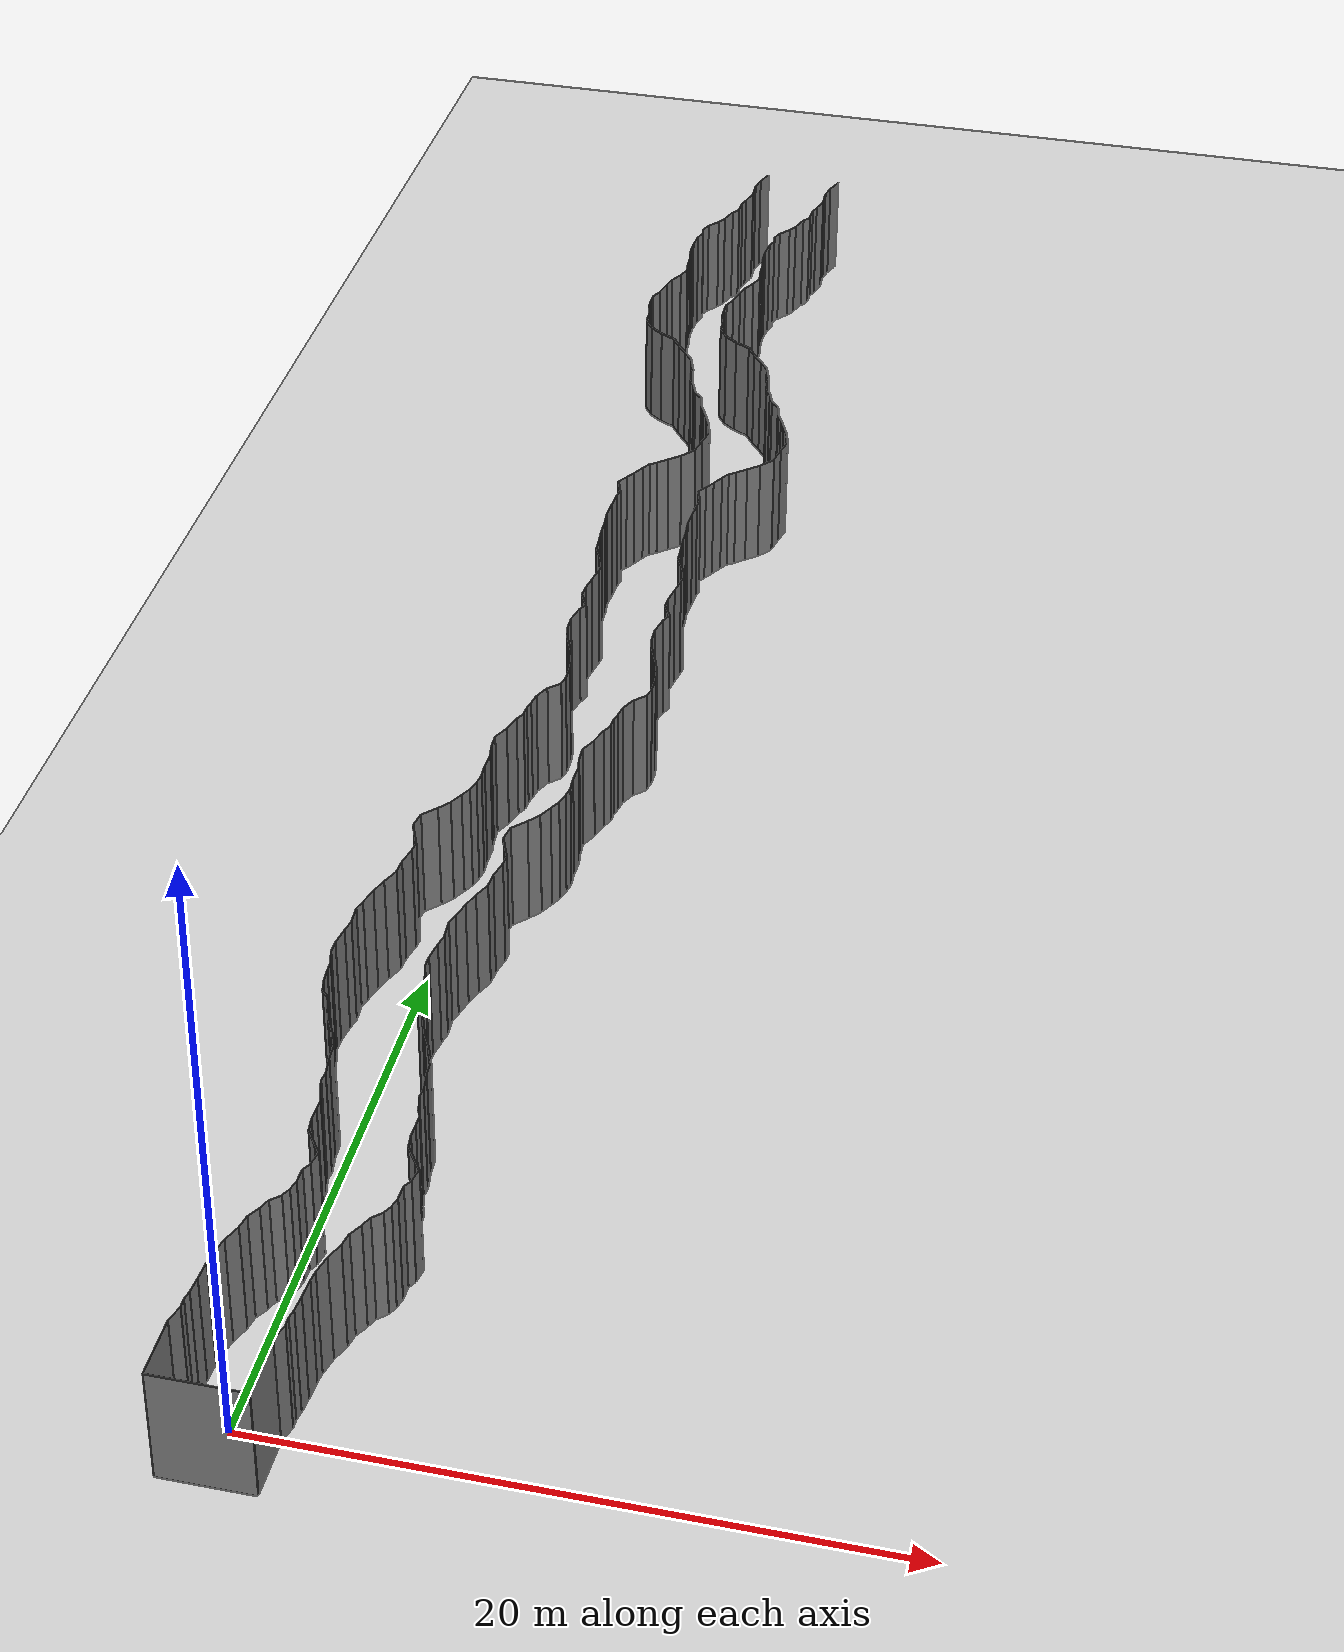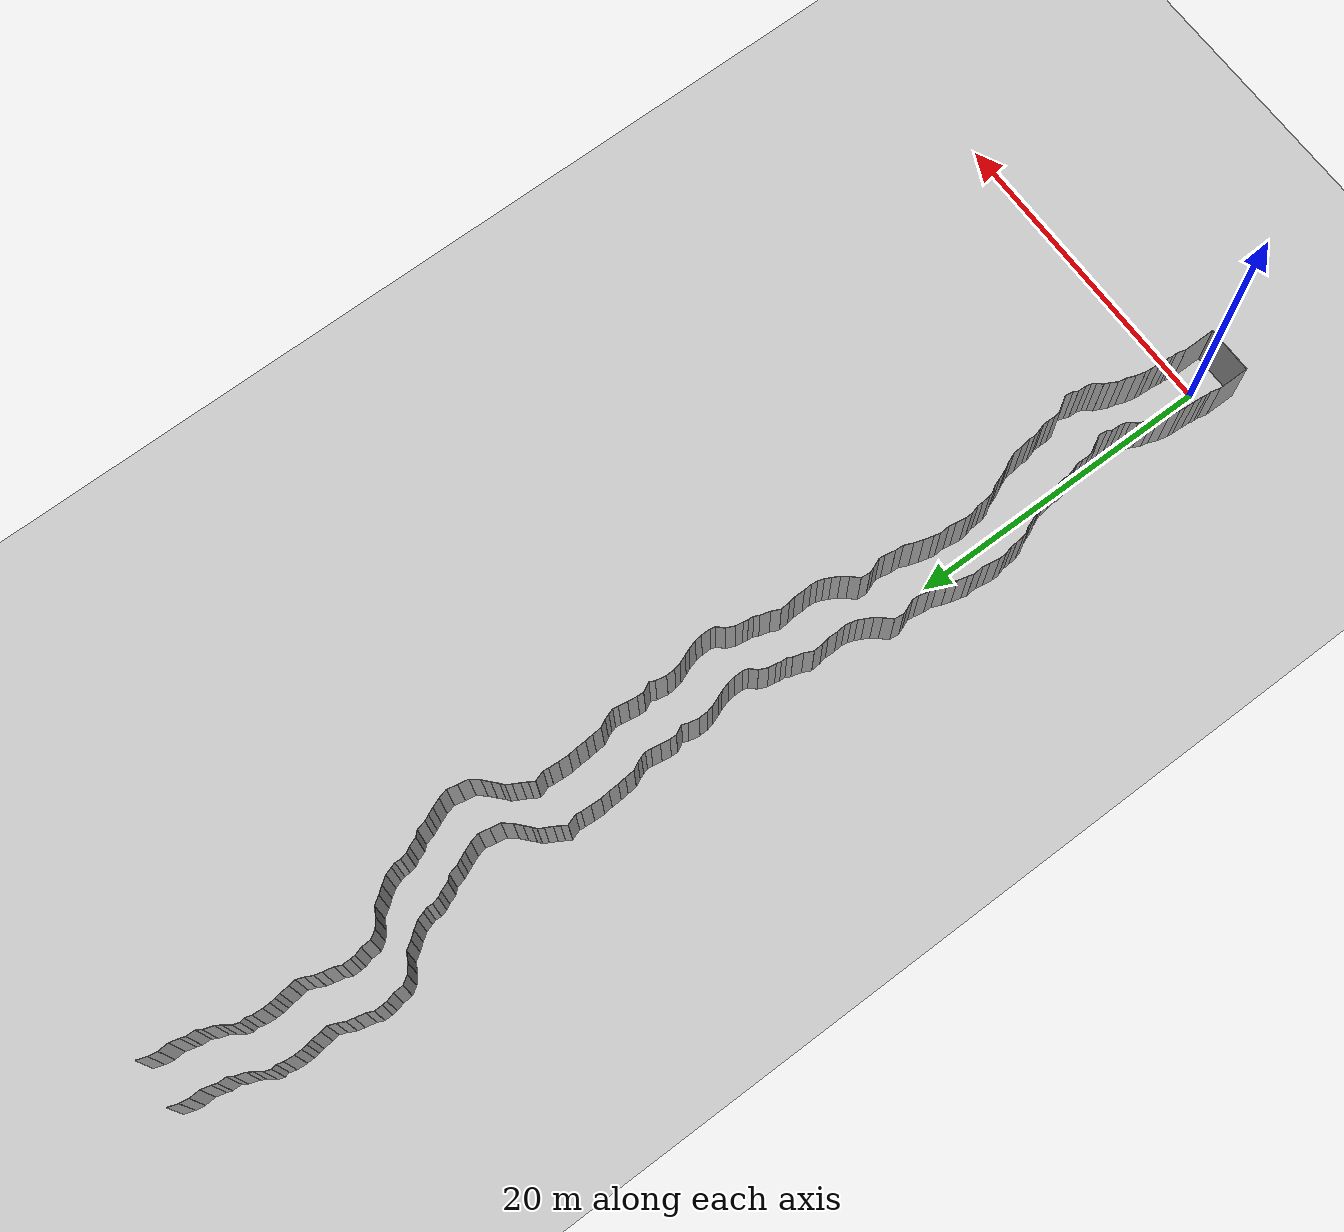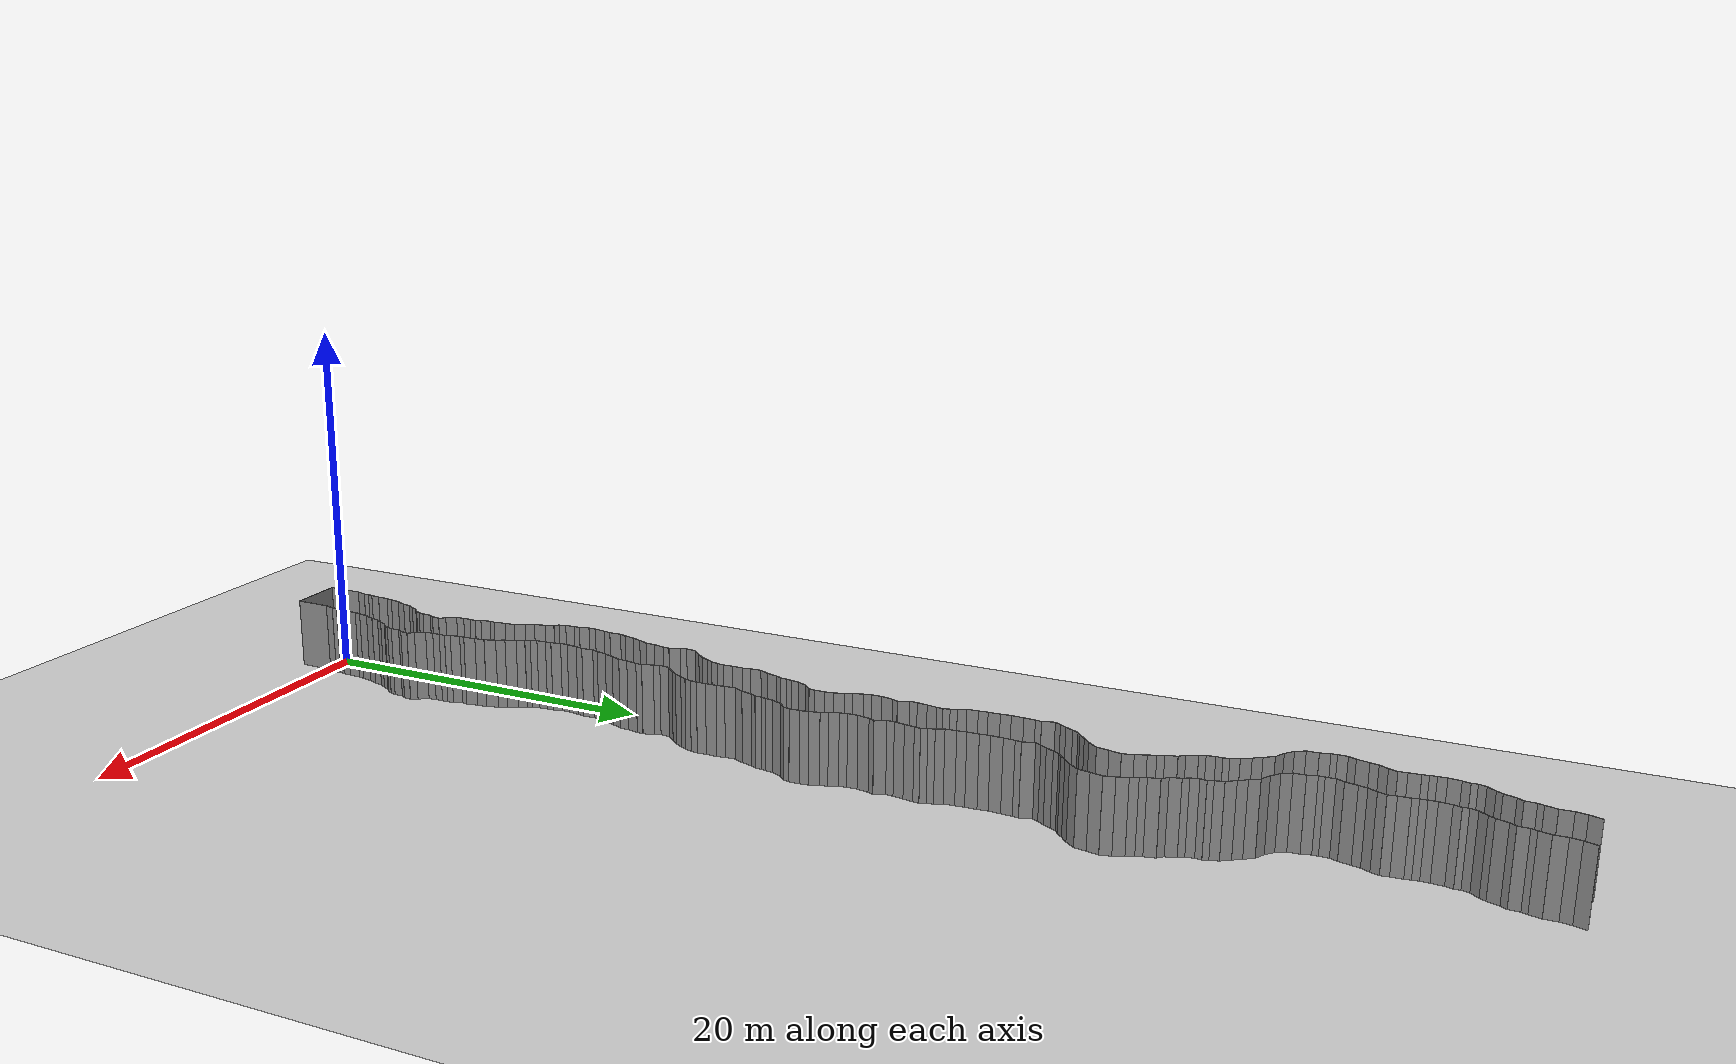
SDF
<sdf version="1.6">
 <world name="default">
  <light name="sun" type="directional">
   <pose>0 0 10 0 -0 0</pose>
   <diffuse>0.8 0.8 0.8 1</diffuse>
   <specular>0.2 0.2 0.2 1</specular>
   <attenuation>
    <range>1000</range>
    <constant>0.9</constant>
    <linear>0.01</linear>
    <quadratic>0.001</quadratic>
   </attenuation>
   <direction>-0.5 0.1 -0.9</direction>
  </light>
  <model name="ground_plane">
   <static>1</static>
   <link name="link">
    <collision name="collision">
     <geometry><plane><normal>0 0 1</normal><size>200 200</size></plane></geometry>
     <surface><friction><ode><mu>100</mu><mu2>50</mu2></ode></friction></surface>
    </collision>
    <visual name="visual">
     <cast_shadows>0</cast_shadows>
     <geometry><plane><normal>0 0 1</normal><size>200 200</size></plane></geometry>
     <material>
      <script><uri>file://media/materials/scripts/gazebo.material</uri><name>Gazebo/Grey</name></script>
     </material>
    </visual>
   </link>
   <pose>0 100 0 0 -0 0</pose>
  </model>
  <gravity>0 0 -9.8</gravity>
  <magnetic_field>6e-06 2.3e-05 -4.2e-05</magnetic_field>
  <atmosphere type="adiabatic"/>
  <physics default="0" name="default_physics" type="ode">
   <max_step_size>0.001</max_step_size>
   <real_time_factor>1</real_time_factor>
   <real_time_update_rate>1000</real_time_update_rate>
  </physics>
  <scene><ambient>0.4 0.4 0.4 1</ambient><background>0.7 0.7 0.7 1</background><shadows>1</shadows></scene>
  <spherical_coordinates>
   <surface_model>EARTH_WGS84</surface_model>
   <latitude_deg>0</latitude_deg>
   <longitude_deg>0</longitude_deg>
   <elevation>0</elevation>
   <heading_deg>0</heading_deg>
  </spherical_coordinates>
  <model name="wall_back">
   <static>1</static>
   <pose>0.0 -2 2 0.0 0 0.0</pose>
   <link name="link">
    <collision name="collision"><geometry><box><size>3 0.02 4</size></box></geometry></collision>
    <visual name="visual">
     <material>
      <script><name>Gazebo/Grey</name><uri>file://media/materials/scripts/gazebo.material</uri></script>
     </material>
     <geometry><box><size>3 0.02 4</size></box></geometry>
    </visual>
   </link>
  </model>
  <model name="wall_left">
   <static>1</static>
   <pose>1.5 -1 2 0 0 0.00</pose>
   <link name="link">
    <collision name="collision"><geometry><box><size>0.02 2 4</size></box></geometry></collision>
    <visual name="visual">
     <material>
      <script><name>Gazebo/Grey</name><uri>file://media/materials/scripts/gazebo.material</uri></script>
     </material>
     <geometry><box><size>0.02 2 4</size></box></geometry>
    </visual>
   </link>
  </model>
  <model name="wall_right">
   <static>1</static>
   <pose>-1.5 -1 2 0 0 0.00</pose>
   <link name="link">
    <collision name="collision"><geometry><box><size>0.02 2 4</size></box></geometry></collision>
    <visual name="visual">
     <material>
      <script><name>Gazebo/Grey</name><uri>file://media/materials/scripts/gazebo.material</uri></script>
     </material>
     <geometry><box><size>0.02 2 4</size></box></geometry>
    </visual>
   </link>
  </model>
  <model name="wall_0">
   <static>1</static>
   <pose>-1.418720931866029 0.2836292645019407 2 0 0 -0.2790887543441646</pose>
   <link name="link">
    <collision name="collision"><geometry><box><size>0.02 0.590090998402 4</size></box></geometry></collision>
    <visual name="visual">
     <material>
      <script><name>Gazebo/Grey</name><uri>file://media/materials/scripts/gazebo.material</uri></script>
     </material>
     <geometry><box><size>0.02 0.590090998402 4</size></box></geometry>
    </visual>
   </link>
  </model>
  <model name="wall_1">
   <static>1</static>
   <pose>1.581279068133971 0.2836292645019407 2 0 0 -0.2790887543441646</pose>
   <link name="link">
    <collision name="collision"><geometry><box><size>0.02 0.590090998402 4</size></box></geometry></collision>
    <visual name="visual">
     <material>
      <script><name>Gazebo/Grey</name><uri>file://media/materials/scripts/gazebo.material</uri></script>
     </material>
     <geometry><box><size>0.02 0.590090998402 4</size></box></geometry>
    </visual>
   </link>
  </model>
  <model name="wall_2">
   <static>1</static>
   <pose>-1.341242303199237 0.7211256952658965 2 0 0 0.0246944621426619</pose>
   <link name="link">
    <collision name="collision"><geometry><box><size>0.02 0.307828187102 4</size></box></geometry></collision>
    <visual name="visual">
     <material>
      <script><name>Gazebo/Grey</name><uri>file://media/materials/scripts/gazebo.material</uri></script>
     </material>
     <geometry><box><size>0.02 0.307828187102 4</size></box></geometry>
    </visual>
   </link>
  </model>
  <model name="wall_3">
   <static>1</static>
   <pose>1.658757696800763 0.7211256952658965 2 0 0 0.0246944621426619</pose>
   <link name="link">
    <collision name="collision"><geometry><box><size>0.02 0.307828187102 4</size></box></geometry></collision>
    <visual name="visual">
     <material>
      <script><name>Gazebo/Grey</name><uri>file://media/materials/scripts/gazebo.material</uri></script>
     </material>
     <geometry><box><size>0.02 0.307828187102 4</size></box></geometry>
    </visual>
   </link>
  </model>
  <model name="wall_4">
   <static>1</static>
   <pose>-1.3144496636133118 1.0261300958018456 2 0 0 -0.19972063417465227</pose>
   <link name="link">
    <collision name="collision"><geometry><box><size>0.02 0.308404929078 4</size></box></geometry></collision>
    <visual name="visual">
     <material>
      <script><name>Gazebo/Grey</name><uri>file://media/materials/scripts/gazebo.material</uri></script>
     </material>
     <geometry><box><size>0.02 0.308404929078 4</size></box></geometry>
    </visual>
   </link>
  </model>
  <model name="wall_5">
   <static>1</static>
   <pose>1.6855503363866882 1.0261300958018456 2 0 0 -0.19972063417465227</pose>
   <link name="link">
    <collision name="collision"><geometry><box><size>0.02 0.308404929078 4</size></box></geometry></collision>
    <visual name="visual">
     <material>
      <script><name>Gazebo/Grey</name><uri>file://media/materials/scripts/gazebo.material</uri></script>
     </material>
     <geometry><box><size>0.02 0.308404929078 4</size></box></geometry>
    </visual>
   </link>
  </model>
  <model name="wall_6">
   <static>1</static>
   <pose>-1.2604508088802011 1.445763980237036 2 0 0 -0.08695362151301869</pose>
   <link name="link">
    <collision name="collision"><geometry><box><size>0.02 0.539029800597 4</size></box></geometry></collision>
    <visual name="visual">
     <material>
      <script><name>Gazebo/Grey</name><uri>file://media/materials/scripts/gazebo.material</uri></script>
     </material>
     <geometry><box><size>0.02 0.539029800597 4</size></box></geometry>
    </visual>
   </link>
  </model>
  <model name="wall_7">
   <static>1</static>
   <pose>1.7395491911197989 1.445763980237036 2 0 0 -0.08695362151301869</pose>
   <link name="link">
    <collision name="collision"><geometry><box><size>0.02 0.539029800597 4</size></box></geometry></collision>
    <visual name="visual">
     <material>
      <script><name>Gazebo/Grey</name><uri>file://media/materials/scripts/gazebo.material</uri></script>
     </material>
     <geometry><box><size>0.02 0.539029800597 4</size></box></geometry>
    </visual>
   </link>
  </model>
  <model name="wall_8">
   <static>1</static>
   <pose>-1.2187104476934287 2.040100968171722 2 0 0 -0.05620934549464021</pose>
   <link name="link">
    <collision name="collision"><geometry><box><size>0.02 0.652711522025 4</size></box></geometry></collision>
    <visual name="visual">
     <material>
      <script><name>Gazebo/Grey</name><uri>file://media/materials/scripts/gazebo.material</uri></script>
     </material>
     <geometry><box><size>0.02 0.652711522025 4</size></box></geometry>
    </visual>
   </link>
  </model>
  <model name="wall_9">
   <static>1</static>
   <pose>1.7812895523065713 2.040100968171722 2 0 0 -0.05620934549464021</pose>
   <link name="link">
    <collision name="collision"><geometry><box><size>0.02 0.652711522025 4</size></box></geometry></collision>
    <visual name="visual">
     <material>
      <script><name>Gazebo/Grey</name><uri>file://media/materials/scripts/gazebo.material</uri></script>
     </material>
     <geometry><box><size>0.02 0.652711522025 4</size></box></geometry>
    </visual>
   </link>
  </model>
  <model name="wall_10">
   <static>1</static>
   <pose>-1.1776914019775158 2.542547777089179 2 0 0 -0.12774689212215662</pose>
   <link name="link">
    <collision name="collision"><geometry><box><size>0.02 0.356114758947 4</size></box></geometry></collision>
    <visual name="visual">
     <material>
      <script><name>Gazebo/Grey</name><uri>file://media/materials/scripts/gazebo.material</uri></script>
     </material>
     <geometry><box><size>0.02 0.356114758947 4</size></box></geometry>
    </visual>
   </link>
  </model>
  <model name="wall_11">
   <static>1</static>
   <pose>1.8223085980224842 2.542547777089179 2 0 0 -0.12774689212215662</pose>
   <link name="link">
    <collision name="collision"><geometry><box><size>0.02 0.356114758947 4</size></box></geometry></collision>
    <visual name="visual">
     <material>
      <script><name>Gazebo/Grey</name><uri>file://media/materials/scripts/gazebo.material</uri></script>
     </material>
     <geometry><box><size>0.02 0.356114758947 4</size></box></geometry>
    </visual>
   </link>
  </model>
  <model name="wall_12">
   <static>1</static>
   <pose>-1.081717537705951 3.026090564731109 2 0 0 -0.23438848789214636</pose>
   <link name="link">
    <collision name="collision"><geometry><box><size>0.02 0.631129904641 4</size></box></geometry></collision>
    <visual name="visual">
     <material>
      <script><name>Gazebo/Grey</name><uri>file://media/materials/scripts/gazebo.material</uri></script>
     </material>
     <geometry><box><size>0.02 0.631129904641 4</size></box></geometry>
    </visual>
   </link>
  </model>
  <model name="wall_13">
   <static>1</static>
   <pose>1.918282462294049 3.026090564731109 2 0 0 -0.23438848789214636</pose>
   <link name="link">
    <collision name="collision"><geometry><box><size>0.02 0.631129904641 4</size></box></geometry></collision>
    <visual name="visual">
     <material>
      <script><name>Gazebo/Grey</name><uri>file://media/materials/scripts/gazebo.material</uri></script>
     </material>
     <geometry><box><size>0.02 0.631129904641 4</size></box></geometry>
    </visual>
   </link>
  </model>
  <model name="wall_14">
   <static>1</static>
   <pose>-0.8934936141048421 3.618917026474115 2 0 0 -0.3822494433582523</pose>
   <link name="link">
    <collision name="collision"><geometry><box><size>0.02 0.616256826104 4</size></box></geometry></collision>
    <visual name="visual">
     <material>
      <script><name>Gazebo/Grey</name><uri>file://media/materials/scripts/gazebo.material</uri></script>
     </material>
     <geometry><box><size>0.02 0.616256826104 4</size></box></geometry>
    </visual>
   </link>
  </model>
  <model name="wall_15">
   <static>1</static>
   <pose>2.106506385895158 3.618917026474115 2 0 0 -0.3822494433582523</pose>
   <link name="link">
    <collision name="collision"><geometry><box><size>0.02 0.616256826104 4</size></box></geometry></collision>
    <visual name="visual">
     <material>
      <script><name>Gazebo/Grey</name><uri>file://media/materials/scripts/gazebo.material</uri></script>
     </material>
     <geometry><box><size>0.02 0.616256826104 4</size></box></geometry>
    </visual>
   </link>
  </model>
  <model name="wall_16">
   <static>1</static>
   <pose>-0.7320691048712408 4.14168421204616 2 0 0 -0.19379887287974368</pose>
   <link name="link">
    <collision name="collision"><geometry><box><size>0.02 0.482792093456 4</size></box></geometry></collision>
    <visual name="visual">
     <material>
      <script><name>Gazebo/Grey</name><uri>file://media/materials/scripts/gazebo.material</uri></script>
     </material>
     <geometry><box><size>0.02 0.482792093456 4</size></box></geometry>
    </visual>
   </link>
  </model>
  <model name="wall_17">
   <static>1</static>
   <pose>2.2679308951287593 4.14168421204616 2 0 0 -0.19379887287974368</pose>
   <link name="link">
    <collision name="collision"><geometry><box><size>0.02 0.482792093456 4</size></box></geometry></collision>
    <visual name="visual">
     <material>
      <script><name>Gazebo/Grey</name><uri>file://media/materials/scripts/gazebo.material</uri></script>
     </material>
     <geometry><box><size>0.02 0.482792093456 4</size></box></geometry>
    </visual>
   </link>
  </model>
  <model name="wall_18">
   <static>1</static>
   <pose>-0.5679835542274407 4.57950595588926 2 0 0 -0.5294761476932589</pose>
   <link name="link">
    <collision name="collision"><geometry><box><size>0.02 0.465650039519 4</size></box></geometry></collision>
    <visual name="visual">
     <material>
      <script><name>Gazebo/Grey</name><uri>file://media/materials/scripts/gazebo.material</uri></script>
     </material>
     <geometry><box><size>0.02 0.465650039519 4</size></box></geometry>
    </visual>
   </link>
  </model>
  <model name="wall_19">
   <static>1</static>
   <pose>2.4320164457725593 4.57950595588926 2 0 0 -0.5294761476932589</pose>
   <link name="link">
    <collision name="collision"><geometry><box><size>0.02 0.465650039519 4</size></box></geometry></collision>
    <visual name="visual">
     <material>
      <script><name>Gazebo/Grey</name><uri>file://media/materials/scripts/gazebo.material</uri></script>
     </material>
     <geometry><box><size>0.02 0.465650039519 4</size></box></geometry>
    </visual>
   </link>
  </model>
  <model name="wall_20">
   <static>1</static>
   <pose>-0.37465027299519155 4.964957302089884 2 0 0 -0.3895147349980935</pose>
   <link name="link">
    <collision name="collision"><geometry><box><size>0.02 0.398892985491 4</size></box></geometry></collision>
    <visual name="visual">
     <material>
      <script><name>Gazebo/Grey</name><uri>file://media/materials/scripts/gazebo.material</uri></script>
     </material>
     <geometry><box><size>0.02 0.398892985491 4</size></box></geometry>
    </visual>
   </link>
  </model>
  <model name="wall_21">
   <static>1</static>
   <pose>2.6253497270048083 4.964957302089884 2 0 0 -0.3895147349980935</pose>
   <link name="link">
    <collision name="collision"><geometry><box><size>0.02 0.398892985491 4</size></box></geometry></collision>
    <visual name="visual">
     <material>
      <script><name>Gazebo/Grey</name><uri>file://media/materials/scripts/gazebo.material</uri></script>
     </material>
     <geometry><box><size>0.02 0.398892985491 4</size></box></geometry>
    </visual>
   </link>
  </model>
  <model name="wall_22">
   <static>1</static>
   <pose>-0.1516064225014584 5.28943249200379 2 0 0 -0.8109346569040694</pose>
   <link name="link">
    <collision name="collision"><geometry><box><size>0.02 0.406400247102 4</size></box></geometry></collision>
    <visual name="visual">
     <material>
      <script><name>Gazebo/Grey</name><uri>file://media/materials/scripts/gazebo.material</uri></script>
     </material>
     <geometry><box><size>0.02 0.406400247102 4</size></box></geometry>
    </visual>
   </link>
  </model>
  <model name="wall_23">
   <static>1</static>
   <pose>2.8483935774985416 5.28943249200379 2 0 0 -0.8109346569040694</pose>
   <link name="link">
    <collision name="collision"><geometry><box><size>0.02 0.406400247102 4</size></box></geometry></collision>
    <visual name="visual">
     <material>
      <script><name>Gazebo/Grey</name><uri>file://media/materials/scripts/gazebo.material</uri></script>
     </material>
     <geometry><box><size>0.02 0.406400247102 4</size></box></geometry>
    </visual>
   </link>
  </model>
  <model name="wall_24">
   <static>1</static>
   <pose>0.06868012121094381 5.569758428065945 2 0 0 -0.479488846273843</pose>
   <link name="link">
    <collision name="collision"><geometry><box><size>0.02 0.316394294227 4</size></box></geometry></collision>
    <visual name="visual">
     <material>
      <script><name>Gazebo/Grey</name><uri>file://media/materials/scripts/gazebo.material</uri></script>
     </material>
     <geometry><box><size>0.02 0.316394294227 4</size></box></geometry>
    </visual>
   </link>
  </model>
  <model name="wall_25">
   <static>1</static>
   <pose>3.068680121210944 5.569758428065945 2 0 0 -0.479488846273843</pose>
   <link name="link">
    <collision name="collision"><geometry><box><size>0.02 0.316394294227 4</size></box></geometry></collision>
    <visual name="visual">
     <material>
      <script><name>Gazebo/Grey</name><uri>file://media/materials/scripts/gazebo.material</uri></script>
     </material>
     <geometry><box><size>0.02 0.316394294227 4</size></box></geometry>
    </visual>
   </link>
  </model>
  <model name="wall_26">
   <static>1</static>
   <pose>0.18593630339768286 5.882404439084906 2 0 0 -0.2515428638181696</pose>
   <link name="link">
    <collision name="collision"><geometry><box><size>0.02 0.355773596701 4</size></box></geometry></collision>
    <visual name="visual">
     <material>
      <script><name>Gazebo/Grey</name><uri>file://media/materials/scripts/gazebo.material</uri></script>
     </material>
     <geometry><box><size>0.02 0.355773596701 4</size></box></geometry>
    </visual>
   </link>
  </model>
  <model name="wall_27">
   <static>1</static>
   <pose>3.185936303397683 5.882404439084906 2 0 0 -0.2515428638181696</pose>
   <link name="link">
    <collision name="collision"><geometry><box><size>0.02 0.355773596701 4</size></box></geometry></collision>
    <visual name="visual">
     <material>
      <script><name>Gazebo/Grey</name><uri>file://media/materials/scripts/gazebo.material</uri></script>
     </material>
     <geometry><box><size>0.02 0.355773596701 4</size></box></geometry>
    </visual>
   </link>
  </model>
  <model name="wall_28">
   <static>1</static>
   <pose>0.2360720560894651 6.31762503841502 2 0 0 -0.022283383387591334</pose>
   <link name="link">
    <collision name="collision"><geometry><box><size>0.02 0.525994539962 4</size></box></geometry></collision>
    <visual name="visual">
     <material>
      <script><name>Gazebo/Grey</name><uri>file://media/materials/scripts/gazebo.material</uri></script>
     </material>
     <geometry><box><size>0.02 0.525994539962 4</size></box></geometry>
    </visual>
   </link>
  </model>
  <model name="wall_29">
   <static>1</static>
   <pose>3.236072056089465 6.31762503841502 2 0 0 -0.022283383387591334</pose>
   <link name="link">
    <collision name="collision"><geometry><box><size>0.02 0.525994539962 4</size></box></geometry></collision>
    <visual name="visual">
     <material>
      <script><name>Gazebo/Grey</name><uri>file://media/materials/scripts/gazebo.material</uri></script>
     </material>
     <geometry><box><size>0.02 0.525994539962 4</size></box></geometry>
    </visual>
   </link>
  </model>
  <model name="wall_30">
   <static>1</static>
   <pose>0.3186466332601202 6.714820561646917 2 0 0 -0.5191043784049728</pose>
   <link name="link">
    <collision name="collision"><geometry><box><size>0.02 0.309269000143 4</size></box></geometry></collision>
    <visual name="visual">
     <material>
      <script><name>Gazebo/Grey</name><uri>file://media/materials/scripts/gazebo.material</uri></script>
     </material>
     <geometry><box><size>0.02 0.309269000143 4</size></box></geometry>
    </visual>
   </link>
  </model>
  <model name="wall_31">
   <static>1</static>
   <pose>3.31864663326012 6.714820561646917 2 0 0 -0.5191043784049728</pose>
   <link name="link">
    <collision name="collision"><geometry><box><size>0.02 0.309269000143 4</size></box></geometry></collision>
    <visual name="visual">
     <material>
      <script><name>Gazebo/Grey</name><uri>file://media/materials/scripts/gazebo.material</uri></script>
     </material>
     <geometry><box><size>0.02 0.309269000143 4</size></box></geometry>
    </visual>
   </link>
  </model>
  <model name="wall_32">
   <static>1</static>
   <pose>0.44110680840713734 7.094676948190866 2 0 0 -0.18415553824389494</pose>
   <link name="link">
    <collision name="collision"><geometry><box><size>0.02 0.499633872167 4</size></box></geometry></collision>
    <visual name="visual">
     <material>
      <script><name>Gazebo/Grey</name><uri>file://media/materials/scripts/gazebo.material</uri></script>
     </material>
     <geometry><box><size>0.02 0.499633872167 4</size></box></geometry>
    </visual>
   </link>
  </model>
  <model name="wall_33">
   <static>1</static>
   <pose>3.4411068084071372 7.094676948190866 2 0 0 -0.18415553824389494</pose>
   <link name="link">
    <collision name="collision"><geometry><box><size>0.02 0.499633872167 4</size></box></geometry></collision>
    <visual name="visual">
     <material>
      <script><name>Gazebo/Grey</name><uri>file://media/materials/scripts/gazebo.material</uri></script>
     </material>
     <geometry><box><size>0.02 0.499633872167 4</size></box></geometry>
    </visual>
   </link>
  </model>
  <model name="wall_34">
   <static>1</static>
   <pose>0.3710584632864408 7.511072558477766 2 0 0 0.5957662532528709</pose>
   <link name="link">
    <collision name="collision"><geometry><box><size>0.02 0.412707255745 4</size></box></geometry></collision>
    <visual name="visual">
     <material>
      <script><name>Gazebo/Grey</name><uri>file://media/materials/scripts/gazebo.material</uri></script>
     </material>
     <geometry><box><size>0.02 0.412707255745 4</size></box></geometry>
    </visual>
   </link>
  </model>
  <model name="wall_35">
   <static>1</static>
   <pose>3.371058463286441 7.511072558477766 2 0 0 0.5957662532528709</pose>
   <link name="link">
    <collision name="collision"><geometry><box><size>0.02 0.412707255745 4</size></box></geometry></collision>
    <visual name="visual">
     <material>
      <script><name>Gazebo/Grey</name><uri>file://media/materials/scripts/gazebo.material</uri></script>
     </material>
     <geometry><box><size>0.02 0.412707255745 4</size></box></geometry>
    </visual>
   </link>
  </model>
  <model name="wall_36">
   <static>1</static>
   <pose>0.08198783122872388 7.944110765561193 2 0 0 0.5839075725368912</pose>
   <link name="link">
    <collision name="collision"><geometry><box><size>0.02 0.628624660765 4</size></box></geometry></collision>
    <visual name="visual">
     <material>
      <script><name>Gazebo/Grey</name><uri>file://media/materials/scripts/gazebo.material</uri></script>
     </material>
     <geometry><box><size>0.02 0.628624660765 4</size></box></geometry>
    </visual>
   </link>
  </model>
  <model name="wall_37">
   <static>1</static>
   <pose>3.081987831228724 7.944110765561193 2 0 0 0.5839075725368912</pose>
   <link name="link">
    <collision name="collision"><geometry><box><size>0.02 0.628624660765 4</size></box></geometry></collision>
    <visual name="visual">
     <material>
      <script><name>Gazebo/Grey</name><uri>file://media/materials/scripts/gazebo.material</uri></script>
     </material>
     <geometry><box><size>0.02 0.628624660765 4</size></box></geometry>
    </visual>
   </link>
  </model>
  <model name="wall_38">
   <static>1</static>
   <pose>-0.1208942620142476 8.43280307115103 2 0 0 0.12999576550273212</pose>
   <link name="link">
    <collision name="collision"><geometry><box><size>0.02 0.456767740686 4</size></box></geometry></collision>
    <visual name="visual">
     <material>
      <script><name>Gazebo/Grey</name><uri>file://media/materials/scripts/gazebo.material</uri></script>
     </material>
     <geometry><box><size>0.02 0.456767740686 4</size></box></geometry>
    </visual>
   </link>
  </model>
  <model name="wall_39">
   <static>1</static>
   <pose>2.8791057379857525 8.43280307115103 2 0 0 0.12999576550273212</pose>
   <link name="link">
    <collision name="collision"><geometry><box><size>0.02 0.456767740686 4</size></box></geometry></collision>
    <visual name="visual">
     <material>
      <script><name>Gazebo/Grey</name><uri>file://media/materials/scripts/gazebo.material</uri></script>
     </material>
     <geometry><box><size>0.02 0.456767740686 4</size></box></geometry>
    </visual>
   </link>
  </model>
  <model name="wall_40">
   <static>1</static>
   <pose>-0.14470207770703444 8.884663603209559 2 0 0 -0.02571517482845136</pose>
   <link name="link">
    <collision name="collision"><geometry><box><size>0.02 0.450956421251 4</size></box></geometry></collision>
    <visual name="visual">
     <material>
      <script><name>Gazebo/Grey</name><uri>file://media/materials/scripts/gazebo.material</uri></script>
     </material>
     <geometry><box><size>0.02 0.450956421251 4</size></box></geometry>
    </visual>
   </link>
  </model>
  <model name="wall_41">
   <static>1</static>
   <pose>2.8552979222929658 8.884663603209559 2 0 0 -0.02571517482845136</pose>
   <link name="link">
    <collision name="collision"><geometry><box><size>0.02 0.450956421251 4</size></box></geometry></collision>
    <visual name="visual">
     <material>
      <script><name>Gazebo/Grey</name><uri>file://media/materials/scripts/gazebo.material</uri></script>
     </material>
     <geometry><box><size>0.02 0.450956421251 4</size></box></geometry>
    </visual>
   </link>
  </model>
  <model name="wall_42">
   <static>1</static>
   <pose>-0.1361101137045613 9.293618188733076 2 0 0 -0.015222890307738816</pose>
   <link name="link">
    <collision name="collision"><geometry><box><size>0.02 0.36714438314 4</size></box></geometry></collision>
    <visual name="visual">
     <material>
      <script><name>Gazebo/Grey</name><uri>file://media/materials/scripts/gazebo.material</uri></script>
     </material>
     <geometry><box><size>0.02 0.36714438314 4</size></box></geometry>
    </visual>
   </link>
  </model>
  <model name="wall_43">
   <static>1</static>
   <pose>2.8638898862954387 9.293618188733076 2 0 0 -0.015222890307738816</pose>
   <link name="link">
    <collision name="collision"><geometry><box><size>0.02 0.36714438314 4</size></box></geometry></collision>
    <visual name="visual">
     <material>
      <script><name>Gazebo/Grey</name><uri>file://media/materials/scripts/gazebo.material</uri></script>
     </material>
     <geometry><box><size>0.02 0.36714438314 4</size></box></geometry>
    </visual>
   </link>
  </model>
  <model name="wall_44">
   <static>1</static>
   <pose>-0.18750570676299488 9.636265953010334 2 0 0 0.32828524645726165</pose>
   <link name="link">
    <collision name="collision"><geometry><box><size>0.02 0.336144966952 4</size></box></geometry></collision>
    <visual name="visual">
     <material>
      <script><name>Gazebo/Grey</name><uri>file://media/materials/scripts/gazebo.material</uri></script>
     </material>
     <geometry><box><size>0.02 0.336144966952 4</size></box></geometry>
    </visual>
   </link>
  </model>
  <model name="wall_45">
   <static>1</static>
   <pose>2.812494293237005 9.636265953010334 2 0 0 0.32828524645726165</pose>
   <link name="link">
    <collision name="collision"><geometry><box><size>0.02 0.336144966952 4</size></box></geometry></collision>
    <visual name="visual">
     <material>
      <script><name>Gazebo/Grey</name><uri>file://media/materials/scripts/gazebo.material</uri></script>
     </material>
     <geometry><box><size>0.02 0.336144966952 4</size></box></geometry>
    </visual>
   </link>
  </model>
  <model name="wall_46">
   <static>1</static>
   <pose>-0.3135103133396091 10.06570339823949 2 0 0 0.25964828594055106</pose>
   <link name="link">
    <collision name="collision"><geometry><box><size>0.02 0.559433218344 4</size></box></geometry></collision>
    <visual name="visual">
     <material>
      <script><name>Gazebo/Grey</name><uri>file://media/materials/scripts/gazebo.material</uri></script>
     </material>
     <geometry><box><size>0.02 0.559433218344 4</size></box></geometry>
    </visual>
   </link>
  </model>
  <model name="wall_47">
   <static>1</static>
   <pose>2.6864896866603907 10.06570339823949 2 0 0 0.25964828594055106</pose>
   <link name="link">
    <collision name="collision"><geometry><box><size>0.02 0.559433218344 4</size></box></geometry></collision>
    <visual name="visual">
     <material>
      <script><name>Gazebo/Grey</name><uri>file://media/materials/scripts/gazebo.material</uri></script>
     </material>
     <geometry><box><size>0.02 0.559433218344 4</size></box></geometry>
    </visual>
   </link>
  </model>
  <model name="wall_48">
   <static>1</static>
   <pose>-0.3648416316606976 10.490997387663707 2 0 0 -0.13142810103255845</pose>
   <link name="link">
    <collision name="collision"><geometry><box><size>0.02 0.31260273687 4</size></box></geometry></collision>
    <visual name="visual">
     <material>
      <script><name>Gazebo/Grey</name><uri>file://media/materials/scripts/gazebo.material</uri></script>
     </material>
     <geometry><box><size>0.02 0.31260273687 4</size></box></geometry>
    </visual>
   </link>
  </model>
  <model name="wall_49">
   <static>1</static>
   <pose>2.6351583683393023 10.490997387663707 2 0 0 -0.13142810103255845</pose>
   <link name="link">
    <collision name="collision"><geometry><box><size>0.02 0.31260273687 4</size></box></geometry></collision>
    <visual name="visual">
     <material>
      <script><name>Gazebo/Grey</name><uri>file://media/materials/scripts/gazebo.material</uri></script>
     </material>
     <geometry><box><size>0.02 0.31260273687 4</size></box></geometry>
    </visual>
   </link>
  </model>
  <model name="wall_50">
   <static>1</static>
   <pose>-0.39534904962786294 10.987076728889372 2 0 0 0.14837909782722633</pose>
   <link name="link">
    <collision name="collision"><geometry><box><size>0.02 0.689831778268 4</size></box></geometry></collision>
    <visual name="visual">
     <material>
      <script><name>Gazebo/Grey</name><uri>file://media/materials/scripts/gazebo.material</uri></script>
     </material>
     <geometry><box><size>0.02 0.689831778268 4</size></box></geometry>
    </visual>
   </link>
  </model>
  <model name="wall_51">
   <static>1</static>
   <pose>2.604650950372137 10.987076728889372 2 0 0 0.14837909782722633</pose>
   <link name="link">
    <collision name="collision"><geometry><box><size>0.02 0.689831778268 4</size></box></geometry></collision>
    <visual name="visual">
     <material>
      <script><name>Gazebo/Grey</name><uri>file://media/materials/scripts/gazebo.material</uri></script>
     </material>
     <geometry><box><size>0.02 0.689831778268 4</size></box></geometry>
    </visual>
   </link>
  </model>
  <model name="wall_52">
   <static>1</static>
   <pose>-0.46240392430929694 11.625128169785427 2 0 0 0.05404893801058919</pose>
   <link name="link">
    <collision name="collision"><geometry><box><size>0.02 0.594719434515 4</size></box></geometry></collision>
    <visual name="visual">
     <material>
      <script><name>Gazebo/Grey</name><uri>file://media/materials/scripts/gazebo.material</uri></script>
     </material>
     <geometry><box><size>0.02 0.594719434515 4</size></box></geometry>
    </visual>
   </link>
  </model>
  <model name="wall_53">
   <static>1</static>
   <pose>2.5375960756907032 11.625128169785427 2 0 0 0.05404893801058919</pose>
   <link name="link">
    <collision name="collision"><geometry><box><size>0.02 0.594719434515 4</size></box></geometry></collision>
    <visual name="visual">
     <material>
      <script><name>Gazebo/Grey</name><uri>file://media/materials/scripts/gazebo.material</uri></script>
     </material>
     <geometry><box><size>0.02 0.594719434515 4</size></box></geometry>
    </visual>
   </link>
  </model>
  <model name="wall_54">
   <static>1</static>
   <pose>-0.6039016225179614 12.224220617842919 2 0 0 0.39346686974307066</pose>
   <link name="link">
    <collision name="collision"><geometry><box><size>0.02 0.654334614815 4</size></box></geometry></collision>
    <visual name="visual">
     <material>
      <script><name>Gazebo/Grey</name><uri>file://media/materials/scripts/gazebo.material</uri></script>
     </material>
     <geometry><box><size>0.02 0.654334614815 4</size></box></geometry>
    </visual>
   </link>
  </model>
  <model name="wall_55">
   <static>1</static>
   <pose>2.396098377482039 12.224220617842919 2 0 0 0.39346686974307066</pose>
   <link name="link">
    <collision name="collision"><geometry><box><size>0.02 0.654334614815 4</size></box></geometry></collision>
    <visual name="visual">
     <material>
      <script><name>Gazebo/Grey</name><uri>file://media/materials/scripts/gazebo.material</uri></script>
     </material>
     <geometry><box><size>0.02 0.654334614815 4</size></box></geometry>
    </visual>
   </link>
  </model>
  <model name="wall_56">
   <static>1</static>
   <pose>-0.8513352987660092 12.756994384910215 2 0 0 0.4866084925481789</pose>
   <link name="link">
    <collision name="collision"><geometry><box><size>0.02 0.521779764378 4</size></box></geometry></collision>
    <visual name="visual">
     <material>
      <script><name>Gazebo/Grey</name><uri>file://media/materials/scripts/gazebo.material</uri></script>
     </material>
     <geometry><box><size>0.02 0.521779764378 4</size></box></geometry>
    </visual>
   </link>
  </model>
  <model name="wall_57">
   <static>1</static>
   <pose>2.148664701233991 12.756994384910215 2 0 0 0.4866084925481789</pose>
   <link name="link">
    <collision name="collision"><geometry><box><size>0.02 0.521779764378 4</size></box></geometry></collision>
    <visual name="visual">
     <material>
      <script><name>Gazebo/Grey</name><uri>file://media/materials/scripts/gazebo.material</uri></script>
     </material>
     <geometry><box><size>0.02 0.521779764378 4</size></box></geometry>
    </visual>
   </link>
  </model>
  <model name="wall_58">
   <static>1</static>
   <pose>-1.0849468537975955 13.286036519430688 2 0 0 0.3578837072870549</pose>
   <link name="link">
    <collision name="collision"><geometry><box><size>0.02 0.637246437981 4</size></box></geometry></collision>
    <visual name="visual">
     <material>
      <script><name>Gazebo/Grey</name><uri>file://media/materials/scripts/gazebo.material</uri></script>
     </material>
     <geometry><box><size>0.02 0.637246437981 4</size></box></geometry>
    </visual>
   </link>
  </model>
  <model name="wall_59">
   <static>1</static>
   <pose>1.9150531462024045 13.286036519430688 2 0 0 0.3578837072870549</pose>
   <link name="link">
    <collision name="collision"><geometry><box><size>0.02 0.637246437981 4</size></box></geometry></collision>
    <visual name="visual">
     <material>
      <script><name>Gazebo/Grey</name><uri>file://media/materials/scripts/gazebo.material</uri></script>
     </material>
     <geometry><box><size>0.02 0.637246437981 4</size></box></geometry>
    </visual>
   </link>
  </model>
  <model name="wall_60">
   <static>1</static>
   <pose>-1.280596533734518 13.817601756969735 2 0 0 0.3459788750249272</pose>
   <link name="link">
    <collision name="collision"><geometry><box><size>0.02 0.495628823316 4</size></box></geometry></collision>
    <visual name="visual">
     <material>
      <script><name>Gazebo/Grey</name><uri>file://media/materials/scripts/gazebo.material</uri></script>
     </material>
     <geometry><box><size>0.02 0.495628823316 4</size></box></geometry>
    </visual>
   </link>
  </model>
  <model name="wall_61">
   <static>1</static>
   <pose>1.719403466265482 13.817601756969735 2 0 0 0.3459788750249272</pose>
   <link name="link">
    <collision name="collision"><geometry><box><size>0.02 0.495628823316 4</size></box></geometry></collision>
    <visual name="visual">
     <material>
      <script><name>Gazebo/Grey</name><uri>file://media/materials/scripts/gazebo.material</uri></script>
     </material>
     <geometry><box><size>0.02 0.495628823316 4</size></box></geometry>
    </visual>
   </link>
  </model>
  <model name="wall_62">
   <static>1</static>
   <pose>-1.465410064922379 14.163779508664936 2 0 0 0.7280651762045668</pose>
   <link name="link">
    <collision name="collision"><geometry><box><size>0.02 0.302889227254 4</size></box></geometry></collision>
    <visual name="visual">
     <material>
      <script><name>Gazebo/Grey</name><uri>file://media/materials/scripts/gazebo.material</uri></script>
     </material>
     <geometry><box><size>0.02 0.302889227254 4</size></box></geometry>
    </visual>
   </link>
  </model>
  <model name="wall_63">
   <static>1</static>
   <pose>1.534589935077621 14.163779508664936 2 0 0 0.7280651762045668</pose>
   <link name="link">
    <collision name="collision"><geometry><box><size>0.02 0.302889227254 4</size></box></geometry></collision>
    <visual name="visual">
     <material>
      <script><name>Gazebo/Grey</name><uri>file://media/materials/scripts/gazebo.material</uri></script>
     </material>
     <geometry><box><size>0.02 0.302889227254 4</size></box></geometry>
    </visual>
   </link>
  </model>
  <model name="wall_64">
   <static>1</static>
   <pose>-1.6151352466515068 14.470949554867856 2 0 0 0.24701081937816363</pose>
   <link name="link">
    <collision name="collision"><geometry><box><size>0.02 0.400397417509 4</size></box></geometry></collision>
    <visual name="visual">
     <material>
      <script><name>Gazebo/Grey</name><uri>file://media/materials/scripts/gazebo.material</uri></script>
     </material>
     <geometry><box><size>0.02 0.400397417509 4</size></box></geometry>
    </visual>
   </link>
  </model>
  <model name="wall_65">
   <static>1</static>
   <pose>1.3848647533484932 14.470949554867856 2 0 0 0.24701081937816363</pose>
   <link name="link">
    <collision name="collision"><geometry><box><size>0.02 0.400397417509 4</size></box></geometry></collision>
    <visual name="visual">
     <material>
      <script><name>Gazebo/Grey</name><uri>file://media/materials/scripts/gazebo.material</uri></script>
     </material>
     <geometry><box><size>0.02 0.400397417509 4</size></box></geometry>
    </visual>
   </link>
  </model>
  <model name="wall_66">
   <static>1</static>
   <pose>-1.6870073452869347 14.930448475773918 2 0 0 0.08616219275630066</pose>
   <link name="link">
    <collision name="collision"><geometry><box><size>0.02 0.532729685182 4</size></box></geometry></collision>
    <visual name="visual">
     <material>
      <script><name>Gazebo/Grey</name><uri>file://media/materials/scripts/gazebo.material</uri></script>
     </material>
     <geometry><box><size>0.02 0.532729685182 4</size></box></geometry>
    </visual>
   </link>
  </model>
  <model name="wall_67">
   <static>1</static>
   <pose>1.3129926547130653 14.930448475773918 2 0 0 0.08616219275630066</pose>
   <link name="link">
    <collision name="collision"><geometry><box><size>0.02 0.532729685182 4</size></box></geometry></collision>
    <visual name="visual">
     <material>
      <script><name>Gazebo/Grey</name><uri>file://media/materials/scripts/gazebo.material</uri></script>
     </material>
     <geometry><box><size>0.02 0.532729685182 4</size></box></geometry>
    </visual>
   </link>
  </model>
  <model name="wall_68">
   <static>1</static>
   <pose>-1.7127930988483557 15.374504505395269 2 0 0 0.016024889436070906</pose>
   <link name="link">
    <collision name="collision"><geometry><box><size>0.02 0.357404512419 4</size></box></geometry></collision>
    <visual name="visual">
     <material>
      <script><name>Gazebo/Grey</name><uri>file://media/materials/scripts/gazebo.material</uri></script>
     </material>
     <geometry><box><size>0.02 0.357404512419 4</size></box></geometry>
    </visual>
   </link>
  </model>
  <model name="wall_69">
   <static>1</static>
   <pose>1.2872069011516443 15.374504505395269 2 0 0 0.016024889436070906</pose>
   <link name="link">
    <collision name="collision"><geometry><box><size>0.02 0.357404512419 4</size></box></geometry></collision>
    <visual name="visual">
     <material>
      <script><name>Gazebo/Grey</name><uri>file://media/materials/scripts/gazebo.material</uri></script>
     </material>
     <geometry><box><size>0.02 0.357404512419 4</size></box></geometry>
    </visual>
   </link>
  </model>
  <model name="wall_70">
   <static>1</static>
   <pose>-1.7919898284809006 15.823410433434017 2 0 0 0.27530539285445566</pose>
   <link name="link">
    <collision name="collision"><geometry><box><size>0.02 0.561601911744 4</size></box></geometry></collision>
    <visual name="visual">
     <material>
      <script><name>Gazebo/Grey</name><uri>file://media/materials/scripts/gazebo.material</uri></script>
     </material>
     <geometry><box><size>0.02 0.561601911744 4</size></box></geometry>
    </visual>
   </link>
  </model>
  <model name="wall_71">
   <static>1</static>
   <pose>1.2080101715190994 15.823410433434017 2 0 0 0.27530539285445566</pose>
   <link name="link">
    <collision name="collision"><geometry><box><size>0.02 0.561601911744 4</size></box></geometry></collision>
    <visual name="visual">
     <material>
      <script><name>Gazebo/Grey</name><uri>file://media/materials/scripts/gazebo.material</uri></script>
     </material>
     <geometry><box><size>0.02 0.561601911744 4</size></box></geometry>
    </visual>
   </link>
  </model>
  <model name="wall_72">
   <static>1</static>
   <pose>-1.866602926774589 16.312448302352205 2 0 0 -0.007860814081408462</pose>
   <link name="link">
    <collision name="collision"><geometry><box><size>0.02 0.437636026162 4</size></box></geometry></collision>
    <visual name="visual">
     <material>
      <script><name>Gazebo/Grey</name><uri>file://media/materials/scripts/gazebo.material</uri></script>
     </material>
     <geometry><box><size>0.02 0.437636026162 4</size></box></geometry>
    </visual>
   </link>
  </model>
  <model name="wall_73">
   <static>1</static>
   <pose>1.133397073225411 16.312448302352205 2 0 0 -0.007860814081408462</pose>
   <link name="link">
    <collision name="collision"><geometry><box><size>0.02 0.437636026162 4</size></box></geometry></collision>
    <visual name="visual">
     <material>
      <script><name>Gazebo/Grey</name><uri>file://media/materials/scripts/gazebo.material</uri></script>
     </material>
     <geometry><box><size>0.02 0.437636026162 4</size></box></geometry>
    </visual>
   </link>
  </model>
  <model name="wall_74">
   <static>1</static>
   <pose>-1.816891280814868 16.852372335375506 2 0 0 -0.14835587828445984</pose>
   <link name="link">
    <collision name="collision"><geometry><box><size>0.02 0.649358480954 4</size></box></geometry></collision>
    <visual name="visual">
     <material>
      <script><name>Gazebo/Grey</name><uri>file://media/materials/scripts/gazebo.material</uri></script>
     </material>
     <geometry><box><size>0.02 0.649358480954 4</size></box></geometry>
    </visual>
   </link>
  </model>
  <model name="wall_75">
   <static>1</static>
   <pose>1.183108719185132 16.852372335375506 2 0 0 -0.14835587828445984</pose>
   <link name="link">
    <collision name="collision"><geometry><box><size>0.02 0.649358480954 4</size></box></geometry></collision>
    <visual name="visual">
     <material>
      <script><name>Gazebo/Grey</name><uri>file://media/materials/scripts/gazebo.material</uri></script>
     </material>
     <geometry><box><size>0.02 0.649358480954 4</size></box></geometry>
    </visual>
   </link>
  </model>
  <model name="wall_76">
   <static>1</static>
   <pose>-1.7247594297939466 17.385581224090693 2 0 0 -0.20518564760319122</pose>
   <link name="link">
    <collision name="collision"><geometry><box><size>0.02 0.433281077273 4</size></box></geometry></collision>
    <visual name="visual">
     <material>
      <script><name>Gazebo/Grey</name><uri>file://media/materials/scripts/gazebo.material</uri></script>
     </material>
     <geometry><box><size>0.02 0.433281077273 4</size></box></geometry>
    </visual>
   </link>
  </model>
  <model name="wall_77">
   <static>1</static>
   <pose>1.2752405702060534 17.385581224090693 2 0 0 -0.20518564760319122</pose>
   <link name="link">
    <collision name="collision"><geometry><box><size>0.02 0.433281077273 4</size></box></geometry></collision>
    <visual name="visual">
     <material>
      <script><name>Gazebo/Grey</name><uri>file://media/materials/scripts/gazebo.material</uri></script>
     </material>
     <geometry><box><size>0.02 0.433281077273 4</size></box></geometry>
    </visual>
   </link>
  </model>
  <model name="wall_78">
   <static>1</static>
   <pose>-1.7038177128958185 17.93762693356233 2 0 0 0.06813553412664795</pose>
   <link name="link">
    <collision name="collision"><geometry><box><size>0.02 0.681480460559 4</size></box></geometry></collision>
    <visual name="visual">
     <material>
      <script><name>Gazebo/Grey</name><uri>file://media/materials/scripts/gazebo.material</uri></script>
     </material>
     <geometry><box><size>0.02 0.681480460559 4</size></box></geometry>
    </visual>
   </link>
  </model>
  <model name="wall_79">
   <static>1</static>
   <pose>1.2961822871041815 17.93762693356233 2 0 0 0.06813553412664795</pose>
   <link name="link">
    <collision name="collision"><geometry><box><size>0.02 0.681480460559 4</size></box></geometry></collision>
    <visual name="visual">
     <material>
      <script><name>Gazebo/Grey</name><uri>file://media/materials/scripts/gazebo.material</uri></script>
     </material>
     <geometry><box><size>0.02 0.681480460559 4</size></box></geometry>
    </visual>
   </link>
  </model>
  <model name="wall_80">
   <static>1</static>
   <pose>-1.6719285623371034 18.453527863143353 2 0 0 -0.30341766661243313</pose>
   <link name="link">
    <collision name="collision"><geometry><box><size>0.02 0.368746664112 4</size></box></geometry></collision>
    <visual name="visual">
     <material>
      <script><name>Gazebo/Grey</name><uri>file://media/materials/scripts/gazebo.material</uri></script>
     </material>
     <geometry><box><size>0.02 0.368746664112 4</size></box></geometry>
    </visual>
   </link>
  </model>
  <model name="wall_81">
   <static>1</static>
   <pose>1.3280714376628966 18.453527863143353 2 0 0 -0.30341766661243313</pose>
   <link name="link">
    <collision name="collision"><geometry><box><size>0.02 0.368746664112 4</size></box></geometry></collision>
    <visual name="visual">
     <material>
      <script><name>Gazebo/Grey</name><uri>file://media/materials/scripts/gazebo.material</uri></script>
     </material>
     <geometry><box><size>0.02 0.368746664112 4</size></box></geometry>
    </visual>
   </link>
  </model>
  <model name="wall_82">
   <static>1</static>
   <pose>-1.5385484765214832 18.93772542409478 2 0 0 -0.24873321032891926</pose>
   <link name="link">
    <collision name="collision"><geometry><box><size>0.02 0.636067406086 4</size></box></geometry></collision>
    <visual name="visual">
     <material>
      <script><name>Gazebo/Grey</name><uri>file://media/materials/scripts/gazebo.material</uri></script>
     </material>
     <geometry><box><size>0.02 0.636067406086 4</size></box></geometry>
    </visual>
   </link>
  </model>
  <model name="wall_83">
   <static>1</static>
   <pose>1.4614515234785168 18.93772542409478 2 0 0 -0.24873321032891926</pose>
   <link name="link">
    <collision name="collision"><geometry><box><size>0.02 0.636067406086 4</size></box></geometry></collision>
    <visual name="visual">
     <material>
      <script><name>Gazebo/Grey</name><uri>file://media/materials/scripts/gazebo.material</uri></script>
     </material>
     <geometry><box><size>0.02 0.636067406086 4</size></box></geometry>
    </visual>
   </link>
  </model>
  <model name="wall_84">
   <static>1</static>
   <pose>-1.3666559243481262 19.520793661944364 2 0 0 -0.32826254191142534</pose>
   <link name="link">
    <collision name="collision"><geometry><box><size>0.02 0.580648352453 4</size></box></geometry></collision>
    <visual name="visual">
     <material>
      <script><name>Gazebo/Grey</name><uri>file://media/materials/scripts/gazebo.material</uri></script>
     </material>
     <geometry><box><size>0.02 0.580648352453 4</size></box></geometry>
    </visual>
   </link>
  </model>
  <model name="wall_85">
   <static>1</static>
   <pose>1.6333440756518738 19.520793661944364 2 0 0 -0.32826254191142534</pose>
   <link name="link">
    <collision name="collision"><geometry><box><size>0.02 0.580648352453 4</size></box></geometry></collision>
    <visual name="visual">
     <material>
      <script><name>Gazebo/Grey</name><uri>file://media/materials/scripts/gazebo.material</uri></script>
     </material>
     <geometry><box><size>0.02 0.580648352453 4</size></box></geometry>
    </visual>
   </link>
  </model>
  <model name="wall_86">
   <static>1</static>
   <pose>-1.1534943885571574 20.078708159199717 2 0 0 -0.3996156804932362</pose>
   <link name="link">
    <collision name="collision"><geometry><box><size>0.02 0.61460972348 4</size></box></geometry></collision>
    <visual name="visual">
     <material>
      <script><name>Gazebo/Grey</name><uri>file://media/materials/scripts/gazebo.material</uri></script>
     </material>
     <geometry><box><size>0.02 0.61460972348 4</size></box></geometry>
    </visual>
   </link>
  </model>
  <model name="wall_87">
   <static>1</static>
   <pose>1.8465056114428426 20.078708159199717 2 0 0 -0.3996156804932362</pose>
   <link name="link">
    <collision name="collision"><geometry><box><size>0.02 0.61460972348 4</size></box></geometry></collision>
    <visual name="visual">
     <material>
      <script><name>Gazebo/Grey</name><uri>file://media/materials/scripts/gazebo.material</uri></script>
     </material>
     <geometry><box><size>0.02 0.61460972348 4</size></box></geometry>
    </visual>
   </link>
  </model>
  <model name="wall_88">
   <static>1</static>
   <pose>-1.0200352657841782 20.6234163929655 2 0 0 -0.05307291815040809</pose>
   <link name="link">
    <collision name="collision"><geometry><box><size>0.02 0.523969251333 4</size></box></geometry></collision>
    <visual name="visual">
     <material>
      <script><name>Gazebo/Grey</name><uri>file://media/materials/scripts/gazebo.material</uri></script>
     </material>
     <geometry><box><size>0.02 0.523969251333 4</size></box></geometry>
    </visual>
   </link>
  </model>
  <model name="wall_89">
   <static>1</static>
   <pose>1.9799647342158218 20.6234163929655 2 0 0 -0.05307291815040809</pose>
   <link name="link">
    <collision name="collision"><geometry><box><size>0.02 0.523969251333 4</size></box></geometry></collision>
    <visual name="visual">
     <material>
      <script><name>Gazebo/Grey</name><uri>file://media/materials/scripts/gazebo.material</uri></script>
     </material>
     <geometry><box><size>0.02 0.523969251333 4</size></box></geometry>
    </visual>
   </link>
  </model>
  <model name="wall_90">
   <static>1</static>
   <pose>-0.9359213044466046 21.20895832871305 2 0 0 -0.21346356043276166</pose>
   <link name="link">
    <collision name="collision"><geometry><box><size>0.02 0.66289816365 4</size></box></geometry></collision>
    <visual name="visual">
     <material>
      <script><name>Gazebo/Grey</name><uri>file://media/materials/scripts/gazebo.material</uri></script>
     </material>
     <geometry><box><size>0.02 0.66289816365 4</size></box></geometry>
    </visual>
   </link>
  </model>
  <model name="wall_91">
   <static>1</static>
   <pose>2.0640786955533956 21.20895832871305 2 0 0 -0.21346356043276166</pose>
   <link name="link">
    <collision name="collision"><geometry><box><size>0.02 0.66289816365 4</size></box></geometry></collision>
    <visual name="visual">
     <material>
      <script><name>Gazebo/Grey</name><uri>file://media/materials/scripts/gazebo.material</uri></script>
     </material>
     <geometry><box><size>0.02 0.66289816365 4</size></box></geometry>
    </visual>
   </link>
  </model>
  <model name="wall_92">
   <static>1</static>
   <pose>-0.848825271861838 21.7216296808396 2 0 0 -0.08919458513395352</pose>
   <link name="link">
    <collision name="collision"><geometry><box><size>0.02 0.378996904809 4</size></box></geometry></collision>
    <visual name="visual">
     <material>
      <script><name>Gazebo/Grey</name><uri>file://media/materials/scripts/gazebo.material</uri></script>
     </material>
     <geometry><box><size>0.02 0.378996904809 4</size></box></geometry>
    </visual>
   </link>
  </model>
  <model name="wall_93">
   <static>1</static>
   <pose>2.151174728138162 21.7216296808396 2 0 0 -0.08919458513395352</pose>
   <link name="link">
    <collision name="collision"><geometry><box><size>0.02 0.378996904809 4</size></box></geometry></collision>
    <visual name="visual">
     <material>
      <script><name>Gazebo/Grey</name><uri>file://media/materials/scripts/gazebo.material</uri></script>
     </material>
     <geometry><box><size>0.02 0.378996904809 4</size></box></geometry>
    </visual>
   </link>
  </model>
  <model name="wall_94">
   <static>1</static>
   <pose>-0.9506635848219495 22.20506602811699 2 0 0 0.38296611381948487</pose>
   <link name="link">
    <collision name="collision"><geometry><box><size>0.02 0.63541134789 4</size></box></geometry></collision>
    <visual name="visual">
     <material>
      <script><name>Gazebo/Grey</name><uri>file://media/materials/scripts/gazebo.material</uri></script>
     </material>
     <geometry><box><size>0.02 0.63541134789 4</size></box></geometry>
    </visual>
   </link>
  </model>
  <model name="wall_95">
   <static>1</static>
   <pose>2.0493364151780504 22.20506602811699 2 0 0 0.38296611381948487</pose>
   <link name="link">
    <collision name="collision"><geometry><box><size>0.02 0.63541134789 4</size></box></geometry></collision>
    <visual name="visual">
     <material>
      <script><name>Gazebo/Grey</name><uri>file://media/materials/scripts/gazebo.material</uri></script>
     </material>
     <geometry><box><size>0.02 0.63541134789 4</size></box></geometry>
    </visual>
   </link>
  </model>
  <model name="wall_96">
   <static>1</static>
   <pose>-1.128340136040836 22.669004803762913 2 0 0 0.3352094430057979</pose>
   <link name="link">
    <collision name="collision"><geometry><box><size>0.02 0.358445750571 4</size></box></geometry></collision>
    <visual name="visual">
     <material>
      <script><name>Gazebo/Grey</name><uri>file://media/materials/scripts/gazebo.material</uri></script>
     </material>
     <geometry><box><size>0.02 0.358445750571 4</size></box></geometry>
    </visual>
   </link>
  </model>
  <model name="wall_97">
   <static>1</static>
   <pose>1.871659863959164 22.669004803762913 2 0 0 0.3352094430057979</pose>
   <link name="link">
    <collision name="collision"><geometry><box><size>0.02 0.358445750571 4</size></box></geometry></collision>
    <visual name="visual">
     <material>
      <script><name>Gazebo/Grey</name><uri>file://media/materials/scripts/gazebo.material</uri></script>
     </material>
     <geometry><box><size>0.02 0.358445750571 4</size></box></geometry>
    </visual>
   </link>
  </model>
  <model name="wall_98">
   <static>1</static>
   <pose>-1.1476938859109487 23.123007606508512 2 0 0 -0.1381966123171406</pose>
   <link name="link">
    <collision name="collision"><geometry><box><size>0.02 0.574992389249 4</size></box></geometry></collision>
    <visual name="visual">
     <material>
      <script><name>Gazebo/Grey</name><uri>file://media/materials/scripts/gazebo.material</uri></script>
     </material>
     <geometry><box><size>0.02 0.574992389249 4</size></box></geometry>
    </visual>
   </link>
  </model>
  <model name="wall_99">
   <static>1</static>
   <pose>1.8523061140890513 23.123007606508512 2 0 0 -0.1381966123171406</pose>
   <link name="link">
    <collision name="collision"><geometry><box><size>0.02 0.574992389249 4</size></box></geometry></collision>
    <visual name="visual">
     <material>
      <script><name>Gazebo/Grey</name><uri>file://media/materials/scripts/gazebo.material</uri></script>
     </material>
     <geometry><box><size>0.02 0.574992389249 4</size></box></geometry>
    </visual>
   </link>
  </model>
  <model name="wall_100">
   <static>1</static>
   <pose>-0.8898212224910662 23.64646604709157 2 0 0 -0.7407091132913584</pose>
   <link name="link">
    <collision name="collision"><geometry><box><size>0.02 0.646900773663 4</size></box></geometry></collision>
    <visual name="visual">
     <material>
      <script><name>Gazebo/Grey</name><uri>file://media/materials/scripts/gazebo.material</uri></script>
     </material>
     <geometry><box><size>0.02 0.646900773663 4</size></box></geometry>
    </visual>
   </link>
  </model>
  <model name="wall_101">
   <static>1</static>
   <pose>2.110178777508934 23.64646604709157 2 0 0 -0.7407091132913584</pose>
   <link name="link">
    <collision name="collision"><geometry><box><size>0.02 0.646900773663 4</size></box></geometry></collision>
    <visual name="visual">
     <material>
      <script><name>Gazebo/Grey</name><uri>file://media/materials/scripts/gazebo.material</uri></script>
     </material>
     <geometry><box><size>0.02 0.646900773663 4</size></box></geometry>
    </visual>
   </link>
  </model>
  <model name="wall_102">
   <static>1</static>
   <pose>-0.5120971764916322 24.076776949423973 2 0 0 -0.6940694454182406</pose>
   <link name="link">
    <collision name="collision"><geometry><box><size>0.02 0.498556838239 4</size></box></geometry></collision>
    <visual name="visual">
     <material>
      <script><name>Gazebo/Grey</name><uri>file://media/materials/scripts/gazebo.material</uri></script>
     </material>
     <geometry><box><size>0.02 0.498556838239 4</size></box></geometry>
    </visual>
   </link>
  </model>
  <model name="wall_103">
   <static>1</static>
   <pose>2.4879028235083678 24.076776949423973 2 0 0 -0.6940694454182406</pose>
   <link name="link">
    <collision name="collision"><geometry><box><size>0.02 0.498556838239 4</size></box></geometry></collision>
    <visual name="visual">
     <material>
      <script><name>Gazebo/Grey</name><uri>file://media/materials/scripts/gazebo.material</uri></script>
     </material>
     <geometry><box><size>0.02 0.498556838239 4</size></box></geometry>
    </visual>
   </link>
  </model>
  <model name="wall_104">
   <static>1</static>
   <pose>-0.23589487045866298 24.494763606191505 2 0 0 -0.47613775009903936</pose>
   <link name="link">
    <collision name="collision"><geometry><box><size>0.02 0.509419800078 4</size></box></geometry></collision>
    <visual name="visual">
     <material>
      <script><name>Gazebo/Grey</name><uri>file://media/materials/scripts/gazebo.material</uri></script>
     </material>
     <geometry><box><size>0.02 0.509419800078 4</size></box></geometry>
    </visual>
   </link>
  </model>
  <model name="wall_105">
   <static>1</static>
   <pose>2.764105129541337 24.494763606191505 2 0 0 -0.47613775009903936</pose>
   <link name="link">
    <collision name="collision"><geometry><box><size>0.02 0.509419800078 4</size></box></geometry></collision>
    <visual name="visual">
     <material>
      <script><name>Gazebo/Grey</name><uri>file://media/materials/scripts/gazebo.material</uri></script>
     </material>
     <geometry><box><size>0.02 0.509419800078 4</size></box></geometry>
    </visual>
   </link>
  </model>
  <model name="wall_106">
   <static>1</static>
   <pose>-0.025162264664440853 24.901973967312856 2 0 0 -0.47931911530710875</pose>
   <link name="link">
    <collision name="collision"><geometry><box><size>0.02 0.407594997462 4</size></box></geometry></collision>
    <visual name="visual">
     <material>
      <script><name>Gazebo/Grey</name><uri>file://media/materials/scripts/gazebo.material</uri></script>
     </material>
     <geometry><box><size>0.02 0.407594997462 4</size></box></geometry>
    </visual>
   </link>
  </model>
  <model name="wall_107">
   <static>1</static>
   <pose>2.974837735335559 24.901973967312856 2 0 0 -0.47931911530710875</pose>
   <link name="link">
    <collision name="collision"><geometry><box><size>0.02 0.407594997462 4</size></box></geometry></collision>
    <visual name="visual">
     <material>
      <script><name>Gazebo/Grey</name><uri>file://media/materials/scripts/gazebo.material</uri></script>
     </material>
     <geometry><box><size>0.02 0.407594997462 4</size></box></geometry>
    </visual>
   </link>
  </model>
  <model name="wall_108">
   <static>1</static>
   <pose>0.1255518096798071 25.27290882169074 2 0 0 -0.28999241722080604</pose>
   <link name="link">
    <collision name="collision"><geometry><box><size>0.02 0.396773820645 4</size></box></geometry></collision>
    <visual name="visual">
     <material>
      <script><name>Gazebo/Grey</name><uri>file://media/materials/scripts/gazebo.material</uri></script>
     </material>
     <geometry><box><size>0.02 0.396773820645 4</size></box></geometry>
    </visual>
   </link>
  </model>
  <model name="wall_109">
   <static>1</static>
   <pose>3.125551809679807 25.27290882169074 2 0 0 -0.28999241722080604</pose>
   <link name="link">
    <collision name="collision"><geometry><box><size>0.02 0.396773820645 4</size></box></geometry></collision>
    <visual name="visual">
     <material>
      <script><name>Gazebo/Grey</name><uri>file://media/materials/scripts/gazebo.material</uri></script>
     </material>
     <geometry><box><size>0.02 0.396773820645 4</size></box></geometry>
    </visual>
   </link>
  </model>
  <model name="wall_110">
   <static>1</static>
   <pose>0.2130686116777172 25.664112194559277 2 0 0 -0.15192360158569937</pose>
   <link name="link">
    <collision name="collision"><geometry><box><size>0.02 0.406886405152 4</size></box></geometry></collision>
    <visual name="visual">
     <material>
      <script><name>Gazebo/Grey</name><uri>file://media/materials/scripts/gazebo.material</uri></script>
     </material>
     <geometry><box><size>0.02 0.406886405152 4</size></box></geometry>
    </visual>
   </link>
  </model>
  <model name="wall_111">
   <static>1</static>
   <pose>3.213068611677717 25.664112194559277 2 0 0 -0.15192360158569937</pose>
   <link name="link">
    <collision name="collision"><geometry><box><size>0.02 0.406886405152 4</size></box></geometry></collision>
    <visual name="visual">
     <material>
      <script><name>Gazebo/Grey</name><uri>file://media/materials/scripts/gazebo.material</uri></script>
     </material>
     <geometry><box><size>0.02 0.406886405152 4</size></box></geometry>
    </visual>
   </link>
  </model>
  <model name="wall_112">
   <static>1</static>
   <pose>0.22561137117624552 26.126721103445817 2 0 0 0.0696602478694238</pose>
   <link name="link">
    <collision name="collision"><geometry><box><size>0.02 0.524289572353 4</size></box></geometry></collision>
    <visual name="visual">
     <material>
      <script><name>Gazebo/Grey</name><uri>file://media/materials/scripts/gazebo.material</uri></script>
     </material>
     <geometry><box><size>0.02 0.524289572353 4</size></box></geometry>
    </visual>
   </link>
  </model>
  <model name="wall_113">
   <static>1</static>
   <pose>3.2256113711762455 26.126721103445817 2 0 0 0.0696602478694238</pose>
   <link name="link">
    <collision name="collision"><geometry><box><size>0.02 0.524289572353 4</size></box></geometry></collision>
    <visual name="visual">
     <material>
      <script><name>Gazebo/Grey</name><uri>file://media/materials/scripts/gazebo.material</uri></script>
     </material>
     <geometry><box><size>0.02 0.524289572353 4</size></box></geometry>
    </visual>
   </link>
  </model>
  <model name="wall_114">
   <static>1</static>
   <pose>0.21384316813217583 26.71216541169848 2 0 0 -0.01999547176088186</pose>
   <link name="link">
    <collision name="collision"><geometry><box><size>0.02 0.648000137586 4</size></box></geometry></collision>
    <visual name="visual">
     <material>
      <script><name>Gazebo/Grey</name><uri>file://media/materials/scripts/gazebo.material</uri></script>
     </material>
     <geometry><box><size>0.02 0.648000137586 4</size></box></geometry>
    </visual>
   </link>
  </model>
  <model name="wall_115">
   <static>1</static>
   <pose>3.213843168132176 26.71216541169848 2 0 0 -0.01999547176088186</pose>
   <link name="link">
    <collision name="collision"><geometry><box><size>0.02 0.648000137586 4</size></box></geometry></collision>
    <visual name="visual">
     <material>
      <script><name>Gazebo/Grey</name><uri>file://media/materials/scripts/gazebo.material</uri></script>
     </material>
     <geometry><box><size>0.02 0.648000137586 4</size></box></geometry>
    </visual>
   </link>
  </model>
  <model name="wall_116">
   <static>1</static>
   <pose>0.1786469160589521 27.261604471830704 2 0 0 0.18274377982499695</pose>
   <link name="link">
    <collision name="collision"><geometry><box><size>0.02 0.458644513933 4</size></box></geometry></collision>
    <visual name="visual">
     <material>
      <script><name>Gazebo/Grey</name><uri>file://media/materials/scripts/gazebo.material</uri></script>
     </material>
     <geometry><box><size>0.02 0.458644513933 4</size></box></geometry>
    </visual>
   </link>
  </model>
  <model name="wall_117">
   <static>1</static>
   <pose>3.178646916058952 27.261604471830704 2 0 0 0.18274377982499695</pose>
   <link name="link">
    <collision name="collision"><geometry><box><size>0.02 0.458644513933 4</size></box></geometry></collision>
    <visual name="visual">
     <material>
      <script><name>Gazebo/Grey</name><uri>file://media/materials/scripts/gazebo.material</uri></script>
     </material>
     <geometry><box><size>0.02 0.458644513933 4</size></box></geometry>
    </visual>
   </link>
  </model>
  <model name="wall_118">
   <static>1</static>
   <pose>0.12147765407679706 27.78610415848084 2 0 0 0.05177682057464743</pose>
   <link name="link">
    <collision name="collision"><geometry><box><size>0.02 0.598794309908 4</size></box></geometry></collision>
    <visual name="visual">
     <material>
      <script><name>Gazebo/Grey</name><uri>file://media/materials/scripts/gazebo.material</uri></script>
     </material>
     <geometry><box><size>0.02 0.598794309908 4</size></box></geometry>
    </visual>
   </link>
  </model>
  <model name="wall_119">
   <static>1</static>
   <pose>3.1214776540767972 27.78610415848084 2 0 0 0.05177682057464743</pose>
   <link name="link">
    <collision name="collision"><geometry><box><size>0.02 0.598794309908 4</size></box></geometry></collision>
    <visual name="visual">
     <material>
      <script><name>Gazebo/Grey</name><uri>file://media/materials/scripts/gazebo.material</uri></script>
     </material>
     <geometry><box><size>0.02 0.598794309908 4</size></box></geometry>
    </visual>
   </link>
  </model>
  <model name="wall_120">
   <static>1</static>
   <pose>0.23464056865283828 28.352089006159584 2 0 0 -0.44905046242438323</pose>
   <link name="link">
    <collision name="collision"><geometry><box><size>0.02 0.592742504045 4</size></box></geometry></collision>
    <visual name="visual">
     <material>
      <script><name>Gazebo/Grey</name><uri>file://media/materials/scripts/gazebo.material</uri></script>
     </material>
     <geometry><box><size>0.02 0.592742504045 4</size></box></geometry>
    </visual>
   </link>
  </model>
  <model name="wall_121">
   <static>1</static>
   <pose>3.2346405686528383 28.352089006159584 2 0 0 -0.44905046242438323</pose>
   <link name="link">
    <collision name="collision"><geometry><box><size>0.02 0.592742504045 4</size></box></geometry></collision>
    <visual name="visual">
     <material>
      <script><name>Gazebo/Grey</name><uri>file://media/materials/scripts/gazebo.material</uri></script>
     </material>
     <geometry><box><size>0.02 0.592742504045 4</size></box></geometry>
    </visual>
   </link>
  </model>
  <model name="wall_122">
   <static>1</static>
   <pose>0.44948920738320963 28.93048766350913 2 0 0 -0.27001681844773645</pose>
   <link name="link">
    <collision name="collision"><geometry><box><size>0.02 0.646234882567 4</size></box></geometry></collision>
    <visual name="visual">
     <material>
      <script><name>Gazebo/Grey</name><uri>file://media/materials/scripts/gazebo.material</uri></script>
     </material>
     <geometry><box><size>0.02 0.646234882567 4</size></box></geometry>
    </visual>
   </link>
  </model>
  <model name="wall_123">
   <static>1</static>
   <pose>3.4494892073832095 28.93048766350913 2 0 0 -0.27001681844773645</pose>
   <link name="link">
    <collision name="collision"><geometry><box><size>0.02 0.646234882567 4</size></box></geometry></collision>
    <visual name="visual">
     <material>
      <script><name>Gazebo/Grey</name><uri>file://media/materials/scripts/gazebo.material</uri></script>
     </material>
     <geometry><box><size>0.02 0.646234882567 4</size></box></geometry>
    </visual>
   </link>
  </model>
  <model name="wall_124">
   <static>1</static>
   <pose>0.6162840777324186 29.3955263917999 2 0 0 -0.4831858729917589</pose>
   <link name="link">
    <collision name="collision"><geometry><box><size>0.02 0.34698057918 4</size></box></geometry></collision>
    <visual name="visual">
     <material>
      <script><name>Gazebo/Grey</name><uri>file://media/materials/scripts/gazebo.material</uri></script>
     </material>
     <geometry><box><size>0.02 0.34698057918 4</size></box></geometry>
    </visual>
   </link>
  </model>
  <model name="wall_125">
   <static>1</static>
   <pose>3.6162840777324186 29.3955263917999 2 0 0 -0.4831858729917589</pose>
   <link name="link">
    <collision name="collision"><geometry><box><size>0.02 0.34698057918 4</size></box></geometry></collision>
    <visual name="visual">
     <material>
      <script><name>Gazebo/Grey</name><uri>file://media/materials/scripts/gazebo.material</uri></script>
     </material>
     <geometry><box><size>0.02 0.34698057918 4</size></box></geometry>
    </visual>
   </link>
  </model>
  <model name="wall_126">
   <static>1</static>
   <pose>0.7058007923226 29.728565086092427 2 0 0 -0.04963689229328334</pose>
   <link name="link">
    <collision name="collision"><geometry><box><size>0.02 0.359261892584 4</size></box></geometry></collision>
    <visual name="visual">
     <material>
      <script><name>Gazebo/Grey</name><uri>file://media/materials/scripts/gazebo.material</uri></script>
     </material>
     <geometry><box><size>0.02 0.359261892584 4</size></box></geometry>
    </visual>
   </link>
  </model>
  <model name="wall_127">
   <static>1</static>
   <pose>3.7058007923226 29.728565086092427 2 0 0 -0.04963689229328334</pose>
   <link name="link">
    <collision name="collision"><geometry><box><size>0.02 0.359261892584 4</size></box></geometry></collision>
    <visual name="visual">
     <material>
      <script><name>Gazebo/Grey</name><uri>file://media/materials/scripts/gazebo.material</uri></script>
     </material>
     <geometry><box><size>0.02 0.359261892584 4</size></box></geometry>
    </visual>
   </link>
  </model>
  <model name="wall_128">
   <static>1</static>
   <pose>0.7498534801259733 30.06112484624256 2 0 0 -0.2255443832553479</pose>
   <link name="link">
    <collision name="collision"><geometry><box><size>0.02 0.314259521103 4</size></box></geometry></collision>
    <visual name="visual">
     <material>
      <script><name>Gazebo/Grey</name><uri>file://media/materials/scripts/gazebo.material</uri></script>
     </material>
     <geometry><box><size>0.02 0.314259521103 4</size></box></geometry>
    </visual>
   </link>
  </model>
  <model name="wall_129">
   <static>1</static>
   <pose>3.7498534801259735 30.06112484624256 2 0 0 -0.2255443832553479</pose>
   <link name="link">
    <collision name="collision"><geometry><box><size>0.02 0.314259521103 4</size></box></geometry></collision>
    <visual name="visual">
     <material>
      <script><name>Gazebo/Grey</name><uri>file://media/materials/scripts/gazebo.material</uri></script>
     </material>
     <geometry><box><size>0.02 0.314259521103 4</size></box></geometry>
    </visual>
   </link>
  </model>
  <model name="wall_130">
   <static>1</static>
   <pose>0.8202940374581777 30.43915812562923 2 0 0 -0.15570215806998922</pose>
   <link name="link">
    <collision name="collision"><geometry><box><size>0.02 0.455273943294 4</size></box></geometry></collision>
    <visual name="visual">
     <material>
      <script><name>Gazebo/Grey</name><uri>file://media/materials/scripts/gazebo.material</uri></script>
     </material>
     <geometry><box><size>0.02 0.455273943294 4</size></box></geometry>
    </visual>
   </link>
  </model>
  <model name="wall_131">
   <static>1</static>
   <pose>3.8202940374581775 30.43915812562923 2 0 0 -0.15570215806998922</pose>
   <link name="link">
    <collision name="collision"><geometry><box><size>0.02 0.455273943294 4</size></box></geometry></collision>
    <visual name="visual">
     <material>
      <script><name>Gazebo/Grey</name><uri>file://media/materials/scripts/gazebo.material</uri></script>
     </material>
     <geometry><box><size>0.02 0.455273943294 4</size></box></geometry>
    </visual>
   </link>
  </model>
  <model name="wall_132">
   <static>1</static>
   <pose>0.9759990664653507 30.929969723993814 2 0 0 -0.4251554060714948</pose>
   <link name="link">
    <collision name="collision"><geometry><box><size>0.02 0.583832663573 4</size></box></geometry></collision>
    <visual name="visual">
     <material>
      <script><name>Gazebo/Grey</name><uri>file://media/materials/scripts/gazebo.material</uri></script>
     </material>
     <geometry><box><size>0.02 0.583832663573 4</size></box></geometry>
    </visual>
   </link>
  </model>
  <model name="wall_133">
   <static>1</static>
   <pose>3.975999066465351 30.929969723993814 2 0 0 -0.4251554060714948</pose>
   <link name="link">
    <collision name="collision"><geometry><box><size>0.02 0.583832663573 4</size></box></geometry></collision>
    <visual name="visual">
     <material>
      <script><name>Gazebo/Grey</name><uri>file://media/materials/scripts/gazebo.material</uri></script>
     </material>
     <geometry><box><size>0.02 0.583832663573 4</size></box></geometry>
    </visual>
   </link>
  </model>
  <model name="wall_134">
   <static>1</static>
   <pose>1.2895685842342366 31.389309117850935 2 0 0 -0.7847618128862949</pose>
   <link name="link">
    <collision name="collision"><geometry><box><size>0.02 0.5467011844 4</size></box></geometry></collision>
    <visual name="visual">
     <material>
      <script><name>Gazebo/Grey</name><uri>file://media/materials/scripts/gazebo.material</uri></script>
     </material>
     <geometry><box><size>0.02 0.5467011844 4</size></box></geometry>
    </visual>
   </link>
  </model>
  <model name="wall_135">
   <static>1</static>
   <pose>4.289568584234237 31.389309117850935 2 0 0 -0.7847618128862949</pose>
   <link name="link">
    <collision name="collision"><geometry><box><size>0.02 0.5467011844 4</size></box></geometry></collision>
    <visual name="visual">
     <material>
      <script><name>Gazebo/Grey</name><uri>file://media/materials/scripts/gazebo.material</uri></script>
     </material>
     <geometry><box><size>0.02 0.5467011844 4</size></box></geometry>
    </visual>
   </link>
  </model>
  <model name="wall_136">
   <static>1</static>
   <pose>1.5207012554433779 31.75293859552379 2 0 0 -0.21946000550123906</pose>
   <link name="link">
    <collision name="collision"><geometry><box><size>0.02 0.348802906399 4</size></box></geometry></collision>
    <visual name="visual">
     <material>
      <script><name>Gazebo/Grey</name><uri>file://media/materials/scripts/gazebo.material</uri></script>
     </material>
     <geometry><box><size>0.02 0.348802906399 4</size></box></geometry>
    </visual>
   </link>
  </model>
  <model name="wall_137">
   <static>1</static>
   <pose>4.520701255443377 31.75293859552379 2 0 0 -0.21946000550123906</pose>
   <link name="link">
    <collision name="collision"><geometry><box><size>0.02 0.348802906399 4</size></box></geometry></collision>
    <visual name="visual">
     <material>
      <script><name>Gazebo/Grey</name><uri>file://media/materials/scripts/gazebo.material</uri></script>
     </material>
     <geometry><box><size>0.02 0.348802906399 4</size></box></geometry>
    </visual>
   </link>
  </model>
  <model name="wall_138">
   <static>1</static>
   <pose>1.55835137744619 32.21424014301017 2 0 0 0.0010908561495219218</pose>
   <link name="link">
    <collision name="collision"><geometry><box><size>0.02 0.5821665204 4</size></box></geometry></collision>
    <visual name="visual">
     <material>
      <script><name>Gazebo/Grey</name><uri>file://media/materials/scripts/gazebo.material</uri></script>
     </material>
     <geometry><box><size>0.02 0.5821665204 4</size></box></geometry>
    </visual>
   </link>
  </model>
  <model name="wall_139">
   <static>1</static>
   <pose>4.55835137744619 32.21424014301017 2 0 0 0.0010908561495219218</pose>
   <link name="link">
    <collision name="collision"><geometry><box><size>0.02 0.5821665204 4</size></box></geometry></collision>
    <visual name="visual">
     <material>
      <script><name>Gazebo/Grey</name><uri>file://media/materials/scripts/gazebo.material</uri></script>
     </material>
     <geometry><box><size>0.02 0.5821665204 4</size></box></geometry>
    </visual>
   </link>
  </model>
  <model name="wall_140">
   <static>1</static>
   <pose>1.5278825649954908 32.739989917627575 2 0 0 0.1277854529049571</pose>
   <link name="link">
    <collision name="collision"><geometry><box><size>0.02 0.473191521953 4</size></box></geometry></collision>
    <visual name="visual">
     <material>
      <script><name>Gazebo/Grey</name><uri>file://media/materials/scripts/gazebo.material</uri></script>
     </material>
     <geometry><box><size>0.02 0.473191521953 4</size></box></geometry>
    </visual>
   </link>
  </model>
  <model name="wall_141">
   <static>1</static>
   <pose>4.52788256499549 32.739989917627575 2 0 0 0.1277854529049571</pose>
   <link name="link">
    <collision name="collision"><geometry><box><size>0.02 0.473191521953 4</size></box></geometry></collision>
    <visual name="visual">
     <material>
      <script><name>Gazebo/Grey</name><uri>file://media/materials/scripts/gazebo.material</uri></script>
     </material>
     <geometry><box><size>0.02 0.473191521953 4</size></box></geometry>
    </visual>
   </link>
  </model>
  <model name="wall_142">
   <static>1</static>
   <pose>1.4132706696853092 33.25752887209525 2 0 0 0.2901555178018054</pose>
   <link name="link">
    <collision name="collision"><geometry><box><size>0.02 0.590424641988 4</size></box></geometry></collision>
    <visual name="visual">
     <material>
      <script><name>Gazebo/Grey</name><uri>file://media/materials/scripts/gazebo.material</uri></script>
     </material>
     <geometry><box><size>0.02 0.590424641988 4</size></box></geometry>
    </visual>
   </link>
  </model>
  <model name="wall_143">
   <static>1</static>
   <pose>4.413270669685309 33.25752887209525 2 0 0 0.2901555178018054</pose>
   <link name="link">
    <collision name="collision"><geometry><box><size>0.02 0.590424641988 4</size></box></geometry></collision>
    <visual name="visual">
     <material>
      <script><name>Gazebo/Grey</name><uri>file://media/materials/scripts/gazebo.material</uri></script>
     </material>
     <geometry><box><size>0.02 0.590424641988 4</size></box></geometry>
    </visual>
   </link>
  </model>
  <model name="wall_144">
   <static>1</static>
   <pose>1.2471854840154069 33.73537947325544 2 0 0 0.3964663121347487</pose>
   <link name="link">
    <collision name="collision"><geometry><box><size>0.02 0.422748727965 4</size></box></geometry></collision>
    <visual name="visual">
     <material>
      <script><name>Gazebo/Grey</name><uri>file://media/materials/scripts/gazebo.material</uri></script>
     </material>
     <geometry><box><size>0.02 0.422748727965 4</size></box></geometry>
    </visual>
   </link>
  </model>
  <model name="wall_145">
   <static>1</static>
   <pose>4.247185484015407 33.73537947325544 2 0 0 0.3964663121347487</pose>
   <link name="link">
    <collision name="collision"><geometry><box><size>0.02 0.422748727965 4</size></box></geometry></collision>
    <visual name="visual">
     <material>
      <script><name>Gazebo/Grey</name><uri>file://media/materials/scripts/gazebo.material</uri></script>
     </material>
     <geometry><box><size>0.02 0.422748727965 4</size></box></geometry>
    </visual>
   </link>
  </model>
  <model name="wall_146">
   <static>1</static>
   <pose>1.066581053795679 34.184890137559485 2 0 0 0.37087443803420506</pose>
   <link name="link">
    <collision name="collision"><geometry><box><size>0.02 0.546200399746 4</size></box></geometry></collision>
    <visual name="visual">
     <material>
      <script><name>Gazebo/Grey</name><uri>file://media/materials/scripts/gazebo.material</uri></script>
     </material>
     <geometry><box><size>0.02 0.546200399746 4</size></box></geometry>
    </visual>
   </link>
  </model>
  <model name="wall_147">
   <static>1</static>
   <pose>4.066581053795679 34.184890137559485 2 0 0 0.37087443803420506</pose>
   <link name="link">
    <collision name="collision"><geometry><box><size>0.02 0.546200399746 4</size></box></geometry></collision>
    <visual name="visual">
     <material>
      <script><name>Gazebo/Grey</name><uri>file://media/materials/scripts/gazebo.material</uri></script>
     </material>
     <geometry><box><size>0.02 0.546200399746 4</size></box></geometry>
    </visual>
   </link>
  </model>
  <model name="wall_148">
   <static>1</static>
   <pose>0.9239204196627675 34.65008082705074 2 0 0 0.20445626135803957</pose>
   <link name="link">
    <collision name="collision"><geometry><box><size>0.02 0.43027876864 4</size></box></geometry></collision>
    <visual name="visual">
     <material>
      <script><name>Gazebo/Grey</name><uri>file://media/materials/scripts/gazebo.material</uri></script>
     </material>
     <geometry><box><size>0.02 0.43027876864 4</size></box></geometry>
    </visual>
   </link>
  </model>
  <model name="wall_149">
   <static>1</static>
   <pose>3.9239204196627675 34.65008082705074 2 0 0 0.20445626135803957</pose>
   <link name="link">
    <collision name="collision"><geometry><box><size>0.02 0.43027876864 4</size></box></geometry></collision>
    <visual name="visual">
     <material>
      <script><name>Gazebo/Grey</name><uri>file://media/materials/scripts/gazebo.material</uri></script>
     </material>
     <geometry><box><size>0.02 0.43027876864 4</size></box></geometry>
    </visual>
   </link>
  </model>
  <model name="wall_150">
   <static>1</static>
   <pose>0.8704913366165888 35.142128719754304 2 0 0 0.03462960774158834</pose>
   <link name="link">
    <collision name="collision"><geometry><box><size>0.02 0.563116680193 4</size></box></geometry></collision>
    <visual name="visual">
     <material>
      <script><name>Gazebo/Grey</name><uri>file://media/materials/scripts/gazebo.material</uri></script>
     </material>
     <geometry><box><size>0.02 0.563116680193 4</size></box></geometry>
    </visual>
   </link>
  </model>
  <model name="wall_151">
   <static>1</static>
   <pose>3.8704913366165887 35.142128719754304 2 0 0 0.03462960774158834</pose>
   <link name="link">
    <collision name="collision"><geometry><box><size>0.02 0.563116680193 4</size></box></geometry></collision>
    <visual name="visual">
     <material>
      <script><name>Gazebo/Grey</name><uri>file://media/materials/scripts/gazebo.material</uri></script>
     </material>
     <geometry><box><size>0.02 0.563116680193 4</size></box></geometry>
    </visual>
   </link>
  </model>
  <model name="wall_152">
   <static>1</static>
   <pose>0.9309304983596671 35.759803084062504 2 0 0 -0.20576052317169233</pose>
   <link name="link">
    <collision name="collision"><geometry><box><size>0.02 0.687062641342 4</size></box></geometry></collision>
    <visual name="visual">
     <material>
      <script><name>Gazebo/Grey</name><uri>file://media/materials/scripts/gazebo.material</uri></script>
     </material>
     <geometry><box><size>0.02 0.687062641342 4</size></box></geometry>
    </visual>
   </link>
  </model>
  <model name="wall_153">
   <static>1</static>
   <pose>3.9309304983596673 35.759803084062504 2 0 0 -0.20576052317169233</pose>
   <link name="link">
    <collision name="collision"><geometry><box><size>0.02 0.687062641342 4</size></box></geometry></collision>
    <visual name="visual">
     <material>
      <script><name>Gazebo/Grey</name><uri>file://media/materials/scripts/gazebo.material</uri></script>
     </material>
     <geometry><box><size>0.02 0.687062641342 4</size></box></geometry>
    </visual>
   </link>
  </model>
  <model name="wall_154">
   <static>1</static>
   <pose>1.0787655183014848 36.25987318850832 2 0 0 -0.44269857589574896</pose>
   <link name="link">
    <collision name="collision"><geometry><box><size>0.02 0.362517630442 4</size></box></geometry></collision>
    <visual name="visual">
     <material>
      <script><name>Gazebo/Grey</name><uri>file://media/materials/scripts/gazebo.material</uri></script>
     </material>
     <geometry><box><size>0.02 0.362517630442 4</size></box></geometry>
    </visual>
   </link>
  </model>
  <model name="wall_155">
   <static>1</static>
   <pose>4.078765518301485 36.25987318850832 2 0 0 -0.44269857589574896</pose>
   <link name="link">
    <collision name="collision"><geometry><box><size>0.02 0.362517630442 4</size></box></geometry></collision>
    <visual name="visual">
     <material>
      <script><name>Gazebo/Grey</name><uri>file://media/materials/scripts/gazebo.material</uri></script>
     </material>
     <geometry><box><size>0.02 0.362517630442 4</size></box></geometry>
    </visual>
   </link>
  </model>
  <model name="wall_156">
   <static>1</static>
   <pose>1.006678137784895 36.70904799699519 2 0 0 0.4831871846608332</pose>
   <link name="link">
    <collision name="collision"><geometry><box><size>0.02 0.644570358523 4</size></box></geometry></collision>
    <visual name="visual">
     <material>
      <script><name>Gazebo/Grey</name><uri>file://media/materials/scripts/gazebo.material</uri></script>
     </material>
     <geometry><box><size>0.02 0.644570358523 4</size></box></geometry>
    </visual>
   </link>
  </model>
  <model name="wall_157">
   <static>1</static>
   <pose>4.0066781377848955 36.70904799699519 2 0 0 0.4831871846608332</pose>
   <link name="link">
    <collision name="collision"><geometry><box><size>0.02 0.644570358523 4</size></box></geometry></collision>
    <visual name="visual">
     <material>
      <script><name>Gazebo/Grey</name><uri>file://media/materials/scripts/gazebo.material</uri></script>
     </material>
     <geometry><box><size>0.02 0.644570358523 4</size></box></geometry>
    </visual>
   </link>
  </model>
  <model name="wall_158">
   <static>1</static>
   <pose>0.8663357798228689 37.20195509348812 2 0 0 -0.045230718924256286</pose>
   <link name="link">
    <collision name="collision"><geometry><box><size>0.02 0.415460028061 4</size></box></geometry></collision>
    <visual name="visual">
     <material>
      <script><name>Gazebo/Grey</name><uri>file://media/materials/scripts/gazebo.material</uri></script>
     </material>
     <geometry><box><size>0.02 0.415460028061 4</size></box></geometry>
    </visual>
   </link>
  </model>
  <model name="wall_159">
   <static>1</static>
   <pose>3.866335779822869 37.20195509348812 2 0 0 -0.045230718924256286</pose>
   <link name="link">
    <collision name="collision"><geometry><box><size>0.02 0.415460028061 4</size></box></geometry></collision>
    <visual name="visual">
     <material>
      <script><name>Gazebo/Grey</name><uri>file://media/materials/scripts/gazebo.material</uri></script>
     </material>
     <geometry><box><size>0.02 0.415460028061 4</size></box></geometry>
    </visual>
   </link>
  </model>
  <model name="wall_160">
   <static>1</static>
   <pose>0.9224930562602742 37.69992433524903 2 0 0 -0.15963679809024692</pose>
   <link name="link">
    <collision name="collision"><geometry><box><size>0.02 0.588384622478 4</size></box></geometry></collision>
    <visual name="visual">
     <material>
      <script><name>Gazebo/Grey</name><uri>file://media/materials/scripts/gazebo.material</uri></script>
     </material>
     <geometry><box><size>0.02 0.588384622478 4</size></box></geometry>
    </visual>
   </link>
  </model>
  <model name="wall_161">
   <static>1</static>
   <pose>3.922493056260274 37.69992433524903 2 0 0 -0.15963679809024692</pose>
   <link name="link">
    <collision name="collision"><geometry><box><size>0.02 0.588384622478 4</size></box></geometry></collision>
    <visual name="visual">
     <material>
      <script><name>Gazebo/Grey</name><uri>file://media/materials/scripts/gazebo.material</uri></script>
     </material>
     <geometry><box><size>0.02 0.588384622478 4</size></box></geometry>
    </visual>
   </link>
  </model>
  <model name="wall_162">
   <static>1</static>
   <pose>1.0173873821105948 38.27496158089008 2 0 0 -0.16753650364621095</pose>
   <link name="link">
    <collision name="collision"><geometry><box><size>0.02 0.577253513264 4</size></box></geometry></collision>
    <visual name="visual">
     <material>
      <script><name>Gazebo/Grey</name><uri>file://media/materials/scripts/gazebo.material</uri></script>
     </material>
     <geometry><box><size>0.02 0.577253513264 4</size></box></geometry>
    </visual>
   </link>
  </model>
  <model name="wall_163">
   <static>1</static>
   <pose>4.017387382110595 38.27496158089008 2 0 0 -0.16753650364621095</pose>
   <link name="link">
    <collision name="collision"><geometry><box><size>0.02 0.577253513264 4</size></box></geometry></collision>
    <visual name="visual">
     <material>
      <script><name>Gazebo/Grey</name><uri>file://media/materials/scripts/gazebo.material</uri></script>
     </material>
     <geometry><box><size>0.02 0.577253513264 4</size></box></geometry>
    </visual>
   </link>
  </model>
  <model name="wall_164">
   <static>1</static>
   <pose>1.0844622152562788 38.731563447598155 2 0 0 -0.10969402421771438</pose>
   <link name="link">
    <collision name="collision"><geometry><box><size>0.02 0.346112865536 4</size></box></geometry></collision>
    <visual name="visual">
     <material>
      <script><name>Gazebo/Grey</name><uri>file://media/materials/scripts/gazebo.material</uri></script>
     </material>
     <geometry><box><size>0.02 0.346112865536 4</size></box></geometry>
    </visual>
   </link>
  </model>
  <model name="wall_165">
   <static>1</static>
   <pose>4.084462215256279 38.731563447598155 2 0 0 -0.10969402421771438</pose>
   <link name="link">
    <collision name="collision"><geometry><box><size>0.02 0.346112865536 4</size></box></geometry></collision>
    <visual name="visual">
     <material>
      <script><name>Gazebo/Grey</name><uri>file://media/materials/scripts/gazebo.material</uri></script>
     </material>
     <geometry><box><size>0.02 0.346112865536 4</size></box></geometry>
    </visual>
   </link>
  </model>
  <model name="wall_166">
   <static>1</static>
   <pose>1.0528176380058856 39.07550781879453 2 0 0 0.2861729953578919</pose>
   <link name="link">
    <collision name="collision"><geometry><box><size>0.02 0.358433188497 4</size></box></geometry></collision>
    <visual name="visual">
     <material>
      <script><name>Gazebo/Grey</name><uri>file://media/materials/scripts/gazebo.material</uri></script>
     </material>
     <geometry><box><size>0.02 0.358433188497 4</size></box></geometry>
    </visual>
   </link>
  </model>
  <model name="wall_167">
   <static>1</static>
   <pose>4.052817638005886 39.07550781879453 2 0 0 0.2861729953578919</pose>
   <link name="link">
    <collision name="collision"><geometry><box><size>0.02 0.358433188497 4</size></box></geometry></collision>
    <visual name="visual">
     <material>
      <script><name>Gazebo/Grey</name><uri>file://media/materials/scripts/gazebo.material</uri></script>
     </material>
     <geometry><box><size>0.02 0.358433188497 4</size></box></geometry>
    </visual>
   </link>
  </model>
  <model name="wall_168">
   <static>1</static>
   <pose>0.9354883147767599 39.416214110200244 2 0 0 0.3765582932644857</pose>
   <link name="link">
    <collision name="collision"><geometry><box><size>0.02 0.362989001935 4</size></box></geometry></collision>
    <visual name="visual">
     <material>
      <script><name>Gazebo/Grey</name><uri>file://media/materials/scripts/gazebo.material</uri></script>
     </material>
     <geometry><box><size>0.02 0.362989001935 4</size></box></geometry>
    </visual>
   </link>
  </model>
  <model name="wall_169">
   <static>1</static>
   <pose>3.9354883147767596 39.416214110200244 2 0 0 0.3765582932644857</pose>
   <link name="link">
    <collision name="collision"><geometry><box><size>0.02 0.362989001935 4</size></box></geometry></collision>
    <visual name="visual">
     <material>
      <script><name>Gazebo/Grey</name><uri>file://media/materials/scripts/gazebo.material</uri></script>
     </material>
     <geometry><box><size>0.02 0.362989001935 4</size></box></geometry>
    </visual>
   </link>
  </model>
  <model name="wall_170">
   <static>1</static>
   <pose>0.757496980346532 39.79883595564514 2 0 0 0.47971478098344517</pose>
   <link name="link">
    <collision name="collision"><geometry><box><size>0.02 0.482103963508 4</size></box></geometry></collision>
    <visual name="visual">
     <material>
      <script><name>Gazebo/Grey</name><uri>file://media/materials/scripts/gazebo.material</uri></script>
     </material>
     <geometry><box><size>0.02 0.482103963508 4</size></box></geometry>
    </visual>
   </link>
  </model>
  <model name="wall_171">
   <static>1</static>
   <pose>3.757496980346532 39.79883595564514 2 0 0 0.47971478098344517</pose>
   <link name="link">
    <collision name="collision"><geometry><box><size>0.02 0.482103963508 4</size></box></geometry></collision>
    <visual name="visual">
     <material>
      <script><name>Gazebo/Grey</name><uri>file://media/materials/scripts/gazebo.material</uri></script>
     </material>
     <geometry><box><size>0.02 0.482103963508 4</size></box></geometry>
    </visual>
   </link>
  </model>
  <model name="wall_172">
   <static>1</static>
   <pose>0.6244893099963778 40.31323860465824 2 0 0 0.07225866777856937</pose>
   <link name="link">
    <collision name="collision"><geometry><box><size>0.02 0.60269078524 4</size></box></geometry></collision>
    <visual name="visual">
     <material>
      <script><name>Gazebo/Grey</name><uri>file://media/materials/scripts/gazebo.material</uri></script>
     </material>
     <geometry><box><size>0.02 0.60269078524 4</size></box></geometry>
    </visual>
   </link>
  </model>
  <model name="wall_173">
   <static>1</static>
   <pose>3.6244893099963775 40.31323860465824 2 0 0 0.07225866777856937</pose>
   <link name="link">
    <collision name="collision"><geometry><box><size>0.02 0.60269078524 4</size></box></geometry></collision>
    <visual name="visual">
     <material>
      <script><name>Gazebo/Grey</name><uri>file://media/materials/scripts/gazebo.material</uri></script>
     </material>
     <geometry><box><size>0.02 0.60269078524 4</size></box></geometry>
    </visual>
   </link>
  </model>
  <model name="wall_174">
   <static>1</static>
   <pose>0.5772567695850367 40.86838111164113 2 0 0 0.09973989840003131</pose>
   <link name="link">
    <collision name="collision"><geometry><box><size>0.02 0.511710112355 4</size></box></geometry></collision>
    <visual name="visual">
     <material>
      <script><name>Gazebo/Grey</name><uri>file://media/materials/scripts/gazebo.material</uri></script>
     </material>
     <geometry><box><size>0.02 0.511710112355 4</size></box></geometry>
    </visual>
   </link>
  </model>
  <model name="wall_175">
   <static>1</static>
   <pose>3.577256769585037 40.86838111164113 2 0 0 0.09973989840003131</pose>
   <link name="link">
    <collision name="collision"><geometry><box><size>0.02 0.511710112355 4</size></box></geometry></collision>
    <visual name="visual">
     <material>
      <script><name>Gazebo/Grey</name><uri>file://media/materials/scripts/gazebo.material</uri></script>
     </material>
     <geometry><box><size>0.02 0.511710112355 4</size></box></geometry>
    </visual>
   </link>
  </model>
  <model name="wall_176">
   <static>1</static>
   <pose>0.539848820118687 41.443198120527285 2 0 0 0.03724083981375796</pose>
   <link name="link">
    <collision name="collision"><geometry><box><size>0.02 0.64091143661 4</size></box></geometry></collision>
    <visual name="visual">
     <material>
      <script><name>Gazebo/Grey</name><uri>file://media/materials/scripts/gazebo.material</uri></script>
     </material>
     <geometry><box><size>0.02 0.64091143661 4</size></box></geometry>
    </visual>
   </link>
  </model>
  <model name="wall_177">
   <static>1</static>
   <pose>3.539848820118687 41.443198120527285 2 0 0 0.03724083981375796</pose>
   <link name="link">
    <collision name="collision"><geometry><box><size>0.02 0.64091143661 4</size></box></geometry></collision>
    <visual name="visual">
     <material>
      <script><name>Gazebo/Grey</name><uri>file://media/materials/scripts/gazebo.material</uri></script>
     </material>
     <geometry><box><size>0.02 0.64091143661 4</size></box></geometry>
    </visual>
   </link>
  </model>
  <model name="wall_178">
   <static>1</static>
   <pose>0.49600251614485014 42.04236264380286 2 0 0 0.11392363111444061</pose>
   <link name="link">
    <collision name="collision"><geometry><box><size>0.02 0.561501804962 4</size></box></geometry></collision>
    <visual name="visual">
     <material>
      <script><name>Gazebo/Grey</name><uri>file://media/materials/scripts/gazebo.material</uri></script>
     </material>
     <geometry><box><size>0.02 0.561501804962 4</size></box></geometry>
    </visual>
   </link>
  </model>
  <model name="wall_179">
   <static>1</static>
   <pose>3.4960025161448502 42.04236264380286 2 0 0 0.11392363111444061</pose>
   <link name="link">
    <collision name="collision"><geometry><box><size>0.02 0.561501804962 4</size></box></geometry></collision>
    <visual name="visual">
     <material>
      <script><name>Gazebo/Grey</name><uri>file://media/materials/scripts/gazebo.material</uri></script>
     </material>
     <geometry><box><size>0.02 0.561501804962 4</size></box></geometry>
    </visual>
   </link>
  </model>
  <model name="wall_180">
   <static>1</static>
   <pose>0.4798855004668867 42.654808596039615 2 0 0 -0.04733283038546878</pose>
   <link name="link">
    <collision name="collision"><geometry><box><size>0.02 0.667777816223 4</size></box></geometry></collision>
    <visual name="visual">
     <material>
      <script><name>Gazebo/Grey</name><uri>file://media/materials/scripts/gazebo.material</uri></script>
     </material>
     <geometry><box><size>0.02 0.667777816223 4</size></box></geometry>
    </visual>
   </link>
  </model>
  <model name="wall_181">
   <static>1</static>
   <pose>3.479885500466887 42.654808596039615 2 0 0 -0.04733283038546878</pose>
   <link name="link">
    <collision name="collision"><geometry><box><size>0.02 0.667777816223 4</size></box></geometry></collision>
    <visual name="visual">
     <material>
      <script><name>Gazebo/Grey</name><uri>file://media/materials/scripts/gazebo.material</uri></script>
     </material>
     <geometry><box><size>0.02 0.667777816223 4</size></box></geometry>
    </visual>
   </link>
  </model>
  <model name="wall_182">
   <static>1</static>
   <pose>0.5116992023763561 43.29828923566824 2 0 0 -0.051623345974134476</pose>
   <link name="link">
    <collision name="collision"><geometry><box><size>0.02 0.620758334482 4</size></box></geometry></collision>
    <visual name="visual">
     <material>
      <script><name>Gazebo/Grey</name><uri>file://media/materials/scripts/gazebo.material</uri></script>
     </material>
     <geometry><box><size>0.02 0.620758334482 4</size></box></geometry>
    </visual>
   </link>
  </model>
  <model name="wall_183">
   <static>1</static>
   <pose>3.5116992023763562 43.29828923566824 2 0 0 -0.051623345974134476</pose>
   <link name="link">
    <collision name="collision"><geometry><box><size>0.02 0.620758334482 4</size></box></geometry></collision>
    <visual name="visual">
     <material>
      <script><name>Gazebo/Grey</name><uri>file://media/materials/scripts/gazebo.material</uri></script>
     </material>
     <geometry><box><size>0.02 0.620758334482 4</size></box></geometry>
    </visual>
   </link>
  </model>
  <model name="wall_184">
   <static>1</static>
   <pose>0.5539174357366535 43.77749502705897 2 0 0 -0.15360504526523366</pose>
   <link name="link">
    <collision name="collision"><geometry><box><size>0.02 0.342512990177 4</size></box></geometry></collision>
    <visual name="visual">
     <material>
      <script><name>Gazebo/Grey</name><uri>file://media/materials/scripts/gazebo.material</uri></script>
     </material>
     <geometry><box><size>0.02 0.342512990177 4</size></box></geometry>
    </visual>
   </link>
  </model>
  <model name="wall_185">
   <static>1</static>
   <pose>3.5539174357366536 43.77749502705897 2 0 0 -0.15360504526523366</pose>
   <link name="link">
    <collision name="collision"><geometry><box><size>0.02 0.342512990177 4</size></box></geometry></collision>
    <visual name="visual">
     <material>
      <script><name>Gazebo/Grey</name><uri>file://media/materials/scripts/gazebo.material</uri></script>
     </material>
     <geometry><box><size>0.02 0.342512990177 4</size></box></geometry>
    </visual>
   </link>
  </model>
  <model name="wall_186">
   <static>1</static>
   <pose>0.46916573424835484 44.26973230173024 2 0 0 0.3308855293030495</pose>
   <link name="link">
    <collision name="collision"><geometry><box><size>0.02 0.683046156625 4</size></box></geometry></collision>
    <visual name="visual">
     <material>
      <script><name>Gazebo/Grey</name><uri>file://media/materials/scripts/gazebo.material</uri></script>
     </material>
     <geometry><box><size>0.02 0.683046156625 4</size></box></geometry>
    </visual>
   </link>
  </model>
  <model name="wall_187">
   <static>1</static>
   <pose>3.469165734248355 44.26973230173024 2 0 0 0.3308855293030495</pose>
   <link name="link">
    <collision name="collision"><geometry><box><size>0.02 0.683046156625 4</size></box></geometry></collision>
    <visual name="visual">
     <material>
      <script><name>Gazebo/Grey</name><uri>file://media/materials/scripts/gazebo.material</uri></script>
     </material>
     <geometry><box><size>0.02 0.683046156625 4</size></box></geometry>
    </visual>
   </link>
  </model>
  <model name="wall_188">
   <static>1</static>
   <pose>0.4645800463227797 44.76147034130841 2 0 0 -0.5624488898382787</pose>
   <link name="link">
    <collision name="collision"><geometry><box><size>0.02 0.398937342985 4</size></box></geometry></collision>
    <visual name="visual">
     <material>
      <script><name>Gazebo/Grey</name><uri>file://media/materials/scripts/gazebo.material</uri></script>
     </material>
     <geometry><box><size>0.02 0.398937342985 4</size></box></geometry>
    </visual>
   </link>
  </model>
  <model name="wall_189">
   <static>1</static>
   <pose>3.4645800463227796 44.76147034130841 2 0 0 -0.5624488898382787</pose>
   <link name="link">
    <collision name="collision"><geometry><box><size>0.02 0.398937342985 4</size></box></geometry></collision>
    <visual name="visual">
     <material>
      <script><name>Gazebo/Grey</name><uri>file://media/materials/scripts/gazebo.material</uri></script>
     </material>
     <geometry><box><size>0.02 0.398937342985 4</size></box></geometry>
    </visual>
   </link>
  </model>
  <model name="wall_190">
   <static>1</static>
   <pose>0.6776395704448512 45.10397498786715 2 0 0 -0.5506501345800691</pose>
   <link name="link">
    <collision name="collision"><geometry><box><size>0.02 0.407807860173 4</size></box></geometry></collision>
    <visual name="visual">
     <material>
      <script><name>Gazebo/Grey</name><uri>file://media/materials/scripts/gazebo.material</uri></script>
     </material>
     <geometry><box><size>0.02 0.407807860173 4</size></box></geometry>
    </visual>
   </link>
  </model>
  <model name="wall_191">
   <static>1</static>
   <pose>3.6776395704448515 45.10397498786715 2 0 0 -0.5506501345800691</pose>
   <link name="link">
    <collision name="collision"><geometry><box><size>0.02 0.407807860173 4</size></box></geometry></collision>
    <visual name="visual">
     <material>
      <script><name>Gazebo/Grey</name><uri>file://media/materials/scripts/gazebo.material</uri></script>
     </material>
     <geometry><box><size>0.02 0.407807860173 4</size></box></geometry>
    </visual>
   </link>
  </model>
  <model name="wall_192">
   <static>1</static>
   <pose>0.8967950665516643 45.490905214644364 2 0 0 -0.48547534107791</pose>
   <link name="link">
    <collision name="collision"><geometry><box><size>0.02 0.482029898406 4</size></box></geometry></collision>
    <visual name="visual">
     <material>
      <script><name>Gazebo/Grey</name><uri>file://media/materials/scripts/gazebo.material</uri></script>
     </material>
     <geometry><box><size>0.02 0.482029898406 4</size></box></geometry>
    </visual>
   </link>
  </model>
  <model name="wall_193">
   <static>1</static>
   <pose>3.896795066551664 45.490905214644364 2 0 0 -0.48547534107791</pose>
   <link name="link">
    <collision name="collision"><geometry><box><size>0.02 0.482029898406 4</size></box></geometry></collision>
    <visual name="visual">
     <material>
      <script><name>Gazebo/Grey</name><uri>file://media/materials/scripts/gazebo.material</uri></script>
     </material>
     <geometry><box><size>0.02 0.482029898406 4</size></box></geometry>
    </visual>
   </link>
  </model>
  <model name="wall_194">
   <static>1</static>
   <pose>1.102490493124489 45.869267710442976 2 0 0 -0.5138052431447958</pose>
   <link name="link">
    <collision name="collision"><geometry><box><size>0.02 0.379377035872 4</size></box></geometry></collision>
    <visual name="visual">
     <material>
      <script><name>Gazebo/Grey</name><uri>file://media/materials/scripts/gazebo.material</uri></script>
     </material>
     <geometry><box><size>0.02 0.379377035872 4</size></box></geometry>
    </visual>
   </link>
  </model>
  <model name="wall_195">
   <static>1</static>
   <pose>4.102490493124489 45.869267710442976 2 0 0 -0.5138052431447958</pose>
   <link name="link">
    <collision name="collision"><geometry><box><size>0.02 0.379377035872 4</size></box></geometry></collision>
    <visual name="visual">
     <material>
      <script><name>Gazebo/Grey</name><uri>file://media/materials/scripts/gazebo.material</uri></script>
     </material>
     <geometry><box><size>0.02 0.379377035872 4</size></box></geometry>
    </visual>
   </link>
  </model>
  <model name="wall_196">
   <static>1</static>
   <pose>1.3170822508846909 46.1229539157399 2 0 0 -0.9407738620319585</pose>
   <link name="link">
    <collision name="collision"><geometry><box><size>0.02 0.300392848914 4</size></box></geometry></collision>
    <visual name="visual">
     <material>
      <script><name>Gazebo/Grey</name><uri>file://media/materials/scripts/gazebo.material</uri></script>
     </material>
     <geometry><box><size>0.02 0.300392848914 4</size></box></geometry>
    </visual>
   </link>
  </model>
  <model name="wall_197">
   <static>1</static>
   <pose>4.317082250884691 46.1229539157399 2 0 0 -0.9407738620319585</pose>
   <link name="link">
    <collision name="collision"><geometry><box><size>0.02 0.300392848914 4</size></box></geometry></collision>
    <visual name="visual">
     <material>
      <script><name>Gazebo/Grey</name><uri>file://media/materials/scripts/gazebo.material</uri></script>
     </material>
     <geometry><box><size>0.02 0.300392848914 4</size></box></geometry>
    </visual>
   </link>
  </model>
  <model name="wall_198">
   <static>1</static>
   <pose>1.615046346363656 46.375535012743676 2 0 0 -0.8221075825544054</pose>
   <link name="link">
    <collision name="collision"><geometry><box><size>0.02 0.482139147676 4</size></box></geometry></collision>
    <visual name="visual">
     <material>
      <script><name>Gazebo/Grey</name><uri>file://media/materials/scripts/gazebo.material</uri></script>
     </material>
     <geometry><box><size>0.02 0.482139147676 4</size></box></geometry>
    </visual>
   </link>
  </model>
  <model name="wall_199">
   <static>1</static>
   <pose>4.6150463463636555 46.375535012743676 2 0 0 -0.8221075825544054</pose>
   <link name="link">
    <collision name="collision"><geometry><box><size>0.02 0.482139147676 4</size></box></geometry></collision>
    <visual name="visual">
     <material>
      <script><name>Gazebo/Grey</name><uri>file://media/materials/scripts/gazebo.material</uri></script>
     </material>
     <geometry><box><size>0.02 0.482139147676 4</size></box></geometry>
    </visual>
   </link>
  </model>
  <model name="wall_200">
   <static>1</static>
   <pose>1.9972519164830225 46.71783413620596 2 0 0 -0.8566514592350649</pose>
   <link name="link">
    <collision name="collision"><geometry><box><size>0.02 0.544170842487 4</size></box></geometry></collision>
    <visual name="visual">
     <material>
      <script><name>Gazebo/Grey</name><uri>file://media/materials/scripts/gazebo.material</uri></script>
     </material>
     <geometry><box><size>0.02 0.544170842487 4</size></box></geometry>
    </visual>
   </link>
  </model>
  <model name="wall_201">
   <static>1</static>
   <pose>4.997251916483022 46.71783413620596 2 0 0 -0.8566514592350649</pose>
   <link name="link">
    <collision name="collision"><geometry><box><size>0.02 0.544170842487 4</size></box></geometry></collision>
    <visual name="visual">
     <material>
      <script><name>Gazebo/Grey</name><uri>file://media/materials/scripts/gazebo.material</uri></script>
     </material>
     <geometry><box><size>0.02 0.544170842487 4</size></box></geometry>
    </visual>
   </link>
  </model>
  <model name="wall_202">
   <static>1</static>
   <pose>2.414025663902798 47.14948832686361 2 0 0 -0.694660070242626</pose>
   <link name="link">
    <collision name="collision"><geometry><box><size>0.02 0.659782520472 4</size></box></geometry></collision>
    <visual name="visual">
     <material>
      <script><name>Gazebo/Grey</name><uri>file://media/materials/scripts/gazebo.material</uri></script>
     </material>
     <geometry><box><size>0.02 0.659782520472 4</size></box></geometry>
    </visual>
   </link>
  </model>
  <model name="wall_203">
   <static>1</static>
   <pose>5.414025663902798 47.14948832686361 2 0 0 -0.694660070242626</pose>
   <link name="link">
    <collision name="collision"><geometry><box><size>0.02 0.659782520472 4</size></box></geometry></collision>
    <visual name="visual">
     <material>
      <script><name>Gazebo/Grey</name><uri>file://media/materials/scripts/gazebo.material</uri></script>
     </material>
     <geometry><box><size>0.02 0.659782520472 4</size></box></geometry>
    </visual>
   </link>
  </model>
  <model name="wall_204">
   <static>1</static>
   <pose>2.6852910926496945 47.73088167485766 2 0 0 -0.18123224474230137</pose>
   <link name="link">
    <collision name="collision"><geometry><box><size>0.02 0.666815572886 4</size></box></geometry></collision>
    <visual name="visual">
     <material>
      <script><name>Gazebo/Grey</name><uri>file://media/materials/scripts/gazebo.material</uri></script>
     </material>
     <geometry><box><size>0.02 0.666815572886 4</size></box></geometry>
    </visual>
   </link>
  </model>
  <model name="wall_205">
   <static>1</static>
   <pose>5.6852910926496945 47.73088167485766 2 0 0 -0.18123224474230137</pose>
   <link name="link">
    <collision name="collision"><geometry><box><size>0.02 0.666815572886 4</size></box></geometry></collision>
    <visual name="visual">
     <material>
      <script><name>Gazebo/Grey</name><uri>file://media/materials/scripts/gazebo.material</uri></script>
     </material>
     <geometry><box><size>0.02 0.666815572886 4</size></box></geometry>
    </visual>
   </link>
  </model>
  <model name="wall_206">
   <static>1</static>
   <pose>2.8138639876377103 48.3840953946392 2 0 0 -0.20750138721146327</pose>
   <link name="link">
    <collision name="collision"><geometry><box><size>0.02 0.664793415483 4</size></box></geometry></collision>
    <visual name="visual">
     <material>
      <script><name>Gazebo/Grey</name><uri>file://media/materials/scripts/gazebo.material</uri></script>
     </material>
     <geometry><box><size>0.02 0.664793415483 4</size></box></geometry>
    </visual>
   </link>
  </model>
  <model name="wall_207">
   <static>1</static>
   <pose>5.81386398763771 48.3840953946392 2 0 0 -0.20750138721146327</pose>
   <link name="link">
    <collision name="collision"><geometry><box><size>0.02 0.664793415483 4</size></box></geometry></collision>
    <visual name="visual">
     <material>
      <script><name>Gazebo/Grey</name><uri>file://media/materials/scripts/gazebo.material</uri></script>
     </material>
     <geometry><box><size>0.02 0.664793415483 4</size></box></geometry>
    </visual>
   </link>
  </model>
  <model name="wall_208">
   <static>1</static>
   <pose>2.8103397212014136 48.99979868704225 2 0 0 0.2430136691927998</pose>
   <link name="link">
    <collision name="collision"><geometry><box><size>0.02 0.598458211011 4</size></box></geometry></collision>
    <visual name="visual">
     <material>
      <script><name>Gazebo/Grey</name><uri>file://media/materials/scripts/gazebo.material</uri></script>
     </material>
     <geometry><box><size>0.02 0.598458211011 4</size></box></geometry>
    </visual>
   </link>
  </model>
  <model name="wall_209">
   <static>1</static>
   <pose>5.810339721201414 48.99979868704225 2 0 0 0.2430136691927998</pose>
   <link name="link">
    <collision name="collision"><geometry><box><size>0.02 0.598458211011 4</size></box></geometry></collision>
    <visual name="visual">
     <material>
      <script><name>Gazebo/Grey</name><uri>file://media/materials/scripts/gazebo.material</uri></script>
     </material>
     <geometry><box><size>0.02 0.598458211011 4</size></box></geometry>
    </visual>
   </link>
  </model>
  <model name="wall_210">
   <static>1</static>
   <pose>2.621835887290903 49.57283613610712 2 0 0 0.39101772349927655</pose>
   <link name="link">
    <collision name="collision"><geometry><box><size>0.02 0.611344318123 4</size></box></geometry></collision>
    <visual name="visual">
     <material>
      <script><name>Gazebo/Grey</name><uri>file://media/materials/scripts/gazebo.material</uri></script>
     </material>
     <geometry><box><size>0.02 0.611344318123 4</size></box></geometry>
    </visual>
   </link>
  </model>
  <model name="wall_211">
   <static>1</static>
   <pose>5.621835887290903 49.57283613610712 2 0 0 0.39101772349927655</pose>
   <link name="link">
    <collision name="collision"><geometry><box><size>0.02 0.611344318123 4</size></box></geometry></collision>
    <visual name="visual">
     <material>
      <script><name>Gazebo/Grey</name><uri>file://media/materials/scripts/gazebo.material</uri></script>
     </material>
     <geometry><box><size>0.02 0.611344318123 4</size></box></geometry>
    </visual>
   </link>
  </model>
  <model name="wall_212">
   <static>1</static>
   <pose>2.4123098290921705 50.06210805698171 2 0 0 0.4229474718860154</pose>
   <link name="link">
    <collision name="collision"><geometry><box><size>0.02 0.453284829392 4</size></box></geometry></collision>
    <visual name="visual">
     <material>
      <script><name>Gazebo/Grey</name><uri>file://media/materials/scripts/gazebo.material</uri></script>
     </material>
     <geometry><box><size>0.02 0.453284829392 4</size></box></geometry>
    </visual>
   </link>
  </model>
  <model name="wall_213">
   <static>1</static>
   <pose>5.4123098290921705 50.06210805698171 2 0 0 0.4229474718860154</pose>
   <link name="link">
    <collision name="collision"><geometry><box><size>0.02 0.453284829392 4</size></box></geometry></collision>
    <visual name="visual">
     <material>
      <script><name>Gazebo/Grey</name><uri>file://media/materials/scripts/gazebo.material</uri></script>
     </material>
     <geometry><box><size>0.02 0.453284829392 4</size></box></geometry>
    </visual>
   </link>
  </model>
  <model name="wall_214">
   <static>1</static>
   <pose>2.237971357265894 50.439329783368144 2 0 0 0.4448906145277738</pose>
   <link name="link">
    <collision name="collision"><geometry><box><size>0.02 0.377884832766 4</size></box></geometry></collision>
    <visual name="visual">
     <material>
      <script><name>Gazebo/Grey</name><uri>file://media/materials/scripts/gazebo.material</uri></script>
     </material>
     <geometry><box><size>0.02 0.377884832766 4</size></box></geometry>
    </visual>
   </link>
  </model>
  <model name="wall_215">
   <static>1</static>
   <pose>5.237971357265894 50.439329783368144 2 0 0 0.4448906145277738</pose>
   <link name="link">
    <collision name="collision"><geometry><box><size>0.02 0.377884832766 4</size></box></geometry></collision>
    <visual name="visual">
     <material>
      <script><name>Gazebo/Grey</name><uri>file://media/materials/scripts/gazebo.material</uri></script>
     </material>
     <geometry><box><size>0.02 0.377884832766 4</size></box></geometry>
    </visual>
   </link>
  </model>
  <model name="wall_216">
   <static>1</static>
   <pose>2.0843783816440236 50.91032754128619 2 0 0 0.2360877761466812</pose>
   <link name="link">
    <collision name="collision"><geometry><box><size>0.02 0.618038945114 4</size></box></geometry></collision>
    <visual name="visual">
     <material>
      <script><name>Gazebo/Grey</name><uri>file://media/materials/scripts/gazebo.material</uri></script>
     </material>
     <geometry><box><size>0.02 0.618038945114 4</size></box></geometry>
    </visual>
   </link>
  </model>
  <model name="wall_217">
   <static>1</static>
   <pose>5.084378381644024 50.91032754128619 2 0 0 0.2360877761466812</pose>
   <link name="link">
    <collision name="collision"><geometry><box><size>0.02 0.618038945114 4</size></box></geometry></collision>
    <visual name="visual">
     <material>
      <script><name>Gazebo/Grey</name><uri>file://media/materials/scripts/gazebo.material</uri></script>
     </material>
     <geometry><box><size>0.02 0.618038945114 4</size></box></geometry>
    </visual>
   </link>
  </model>
  <model name="wall_218">
   <static>1</static>
   <pose>1.865557092796871 51.360063636584506 2 0 0 0.7761118054766024</pose>
   <link name="link">
    <collision name="collision"><geometry><box><size>0.02 0.418384955539 4</size></box></geometry></collision>
    <visual name="visual">
     <material>
      <script><name>Gazebo/Grey</name><uri>file://media/materials/scripts/gazebo.material</uri></script>
     </material>
     <geometry><box><size>0.02 0.418384955539 4</size></box></geometry>
    </visual>
   </link>
  </model>
  <model name="wall_219">
   <static>1</static>
   <pose>4.865557092796871 51.360063636584506 2 0 0 0.7761118054766024</pose>
   <link name="link">
    <collision name="collision"><geometry><box><size>0.02 0.418384955539 4</size></box></geometry></collision>
    <visual name="visual">
     <material>
      <script><name>Gazebo/Grey</name><uri>file://media/materials/scripts/gazebo.material</uri></script>
     </material>
     <geometry><box><size>0.02 0.418384955539 4</size></box></geometry>
    </visual>
   </link>
  </model>
  <model name="wall_220">
   <static>1</static>
   <pose>1.6194088206359774 51.78997128110106 2 0 0 0.34108146024513536</pose>
   <link name="link">
    <collision name="collision"><geometry><box><size>0.02 0.595545243056 4</size></box></geometry></collision>
    <visual name="visual">
     <material>
      <script><name>Gazebo/Grey</name><uri>file://media/materials/scripts/gazebo.material</uri></script>
     </material>
     <geometry><box><size>0.02 0.595545243056 4</size></box></geometry>
    </visual>
   </link>
  </model>
  <model name="wall_221">
   <static>1</static>
   <pose>4.619408820635977 51.78997128110106 2 0 0 0.34108146024513536</pose>
   <link name="link">
    <collision name="collision"><geometry><box><size>0.02 0.595545243056 4</size></box></geometry></collision>
    <visual name="visual">
     <material>
      <script><name>Gazebo/Grey</name><uri>file://media/materials/scripts/gazebo.material</uri></script>
     </material>
     <geometry><box><size>0.02 0.595545243056 4</size></box></geometry>
    </visual>
   </link>
  </model>
  <model name="wall_222">
   <static>1</static>
   <pose>1.4282915338617492 52.22529554415596 2 0 0 0.5341568054962005</pose>
   <link name="link">
    <collision name="collision"><geometry><box><size>0.02 0.359487886103 4</size></box></geometry></collision>
    <visual name="visual">
     <material>
      <script><name>Gazebo/Grey</name><uri>file://media/materials/scripts/gazebo.material</uri></script>
     </material>
     <geometry><box><size>0.02 0.359487886103 4</size></box></geometry>
    </visual>
   </link>
  </model>
  <model name="wall_223">
   <static>1</static>
   <pose>4.428291533861749 52.22529554415596 2 0 0 0.5341568054962005</pose>
   <link name="link">
    <collision name="collision"><geometry><box><size>0.02 0.359487886103 4</size></box></geometry></collision>
    <visual name="visual">
     <material>
      <script><name>Gazebo/Grey</name><uri>file://media/materials/scripts/gazebo.material</uri></script>
     </material>
     <geometry><box><size>0.02 0.359487886103 4</size></box></geometry>
    </visual>
   </link>
  </model>
  <model name="wall_224">
   <static>1</static>
   <pose>1.2848400152276431 52.6012489202789 2 0 0 0.23058833678077686</pose>
   <link name="link">
    <collision name="collision"><geometry><box><size>0.02 0.454526532368 4</size></box></geometry></collision>
    <visual name="visual">
     <material>
      <script><name>Gazebo/Grey</name><uri>file://media/materials/scripts/gazebo.material</uri></script>
     </material>
     <geometry><box><size>0.02 0.454526532368 4</size></box></geometry>
    </visual>
   </link>
  </model>
  <model name="wall_225">
   <static>1</static>
   <pose>4.284840015227643 52.6012489202789 2 0 0 0.23058833678077686</pose>
   <link name="link">
    <collision name="collision"><geometry><box><size>0.02 0.454526532368 4</size></box></geometry></collision>
    <visual name="visual">
     <material>
      <script><name>Gazebo/Grey</name><uri>file://media/materials/scripts/gazebo.material</uri></script>
     </material>
     <geometry><box><size>0.02 0.454526532368 4</size></box></geometry>
    </visual>
   </link>
  </model>
  <model name="wall_226">
   <static>1</static>
   <pose>1.2480841859718759 52.9963820406396 2 0 0 -0.08710834320790582</pose>
   <link name="link">
    <collision name="collision"><geometry><box><size>0.02 0.349093671941 4</size></box></geometry></collision>
    <visual name="visual">
     <material>
      <script><name>Gazebo/Grey</name><uri>file://media/materials/scripts/gazebo.material</uri></script>
     </material>
     <geometry><box><size>0.02 0.349093671941 4</size></box></geometry>
    </visual>
   </link>
  </model>
  <model name="wall_227">
   <static>1</static>
   <pose>4.248084185971876 52.9963820406396 2 0 0 -0.08710834320790582</pose>
   <link name="link">
    <collision name="collision"><geometry><box><size>0.02 0.349093671941 4</size></box></geometry></collision>
    <visual name="visual">
     <material>
      <script><name>Gazebo/Grey</name><uri>file://media/materials/scripts/gazebo.material</uri></script>
     </material>
     <geometry><box><size>0.02 0.349093671941 4</size></box></geometry>
    </visual>
   </link>
  </model>
  <model name="wall_228">
   <static>1</static>
   <pose>1.2126762462406566 53.32029411449146 2 0 0 0.3252509699786831</pose>
   <link name="link">
    <collision name="collision"><geometry><box><size>0.02 0.316656182492 4</size></box></geometry></collision>
    <visual name="visual">
     <material>
      <script><name>Gazebo/Grey</name><uri>file://media/materials/scripts/gazebo.material</uri></script>
     </material>
     <geometry><box><size>0.02 0.316656182492 4</size></box></geometry>
    </visual>
   </link>
  </model>
  <model name="wall_229">
   <static>1</static>
   <pose>4.212676246240656 53.32029411449146 2 0 0 0.3252509699786831</pose>
   <link name="link">
    <collision name="collision"><geometry><box><size>0.02 0.316656182492 4</size></box></geometry></collision>
    <visual name="visual">
     <material>
      <script><name>Gazebo/Grey</name><uri>file://media/materials/scripts/gazebo.material</uri></script>
     </material>
     <geometry><box><size>0.02 0.316656182492 4</size></box></geometry>
    </visual>
   </link>
  </model>
  <model name="wall_230">
   <static>1</static>
   <pose>1.0893941842021748 53.70084352382923 2 0 0 0.3054540564190224</pose>
   <link name="link">
    <collision name="collision"><geometry><box><size>0.02 0.483422108263 4</size></box></geometry></collision>
    <visual name="visual">
     <material>
      <script><name>Gazebo/Grey</name><uri>file://media/materials/scripts/gazebo.material</uri></script>
     </material>
     <geometry><box><size>0.02 0.483422108263 4</size></box></geometry>
    </visual>
   </link>
  </model>
  <model name="wall_231">
   <static>1</static>
   <pose>4.089394184202175 53.70084352382923 2 0 0 0.3054540564190224</pose>
   <link name="link">
    <collision name="collision"><geometry><box><size>0.02 0.483422108263 4</size></box></geometry></collision>
    <visual name="visual">
     <material>
      <script><name>Gazebo/Grey</name><uri>file://media/materials/scripts/gazebo.material</uri></script>
     </material>
     <geometry><box><size>0.02 0.483422108263 4</size></box></geometry>
    </visual>
   </link>
  </model>
  <model name="wall_232">
   <static>1</static>
   <pose>0.8500264611369097 54.17239151616837 2 0 0 0.6050255382293486</pose>
   <link name="link">
    <collision name="collision"><geometry><box><size>0.02 0.586089393159 4</size></box></geometry></collision>
    <visual name="visual">
     <material>
      <script><name>Gazebo/Grey</name><uri>file://media/materials/scripts/gazebo.material</uri></script>
     </material>
     <geometry><box><size>0.02 0.586089393159 4</size></box></geometry>
    </visual>
   </link>
  </model>
  <model name="wall_233">
   <static>1</static>
   <pose>3.8500264611369097 54.17239151616837 2 0 0 0.6050255382293486</pose>
   <link name="link">
    <collision name="collision"><geometry><box><size>0.02 0.586089393159 4</size></box></geometry></collision>
    <visual name="visual">
     <material>
      <script><name>Gazebo/Grey</name><uri>file://media/materials/scripts/gazebo.material</uri></script>
     </material>
     <geometry><box><size>0.02 0.586089393159 4</size></box></geometry>
    </visual>
   </link>
  </model>
  <model name="wall_234">
   <static>1</static>
   <pose>0.512108124791644 54.63165043639537 2 0 0 0.6653185462518619</pose>
   <link name="link">
    <collision name="collision"><geometry><box><size>0.02 0.554792679324 4</size></box></geometry></collision>
    <visual name="visual">
     <material>
      <script><name>Gazebo/Grey</name><uri>file://media/materials/scripts/gazebo.material</uri></script>
     </material>
     <geometry><box><size>0.02 0.554792679324 4</size></box></geometry>
    </visual>
   </link>
  </model>
  <model name="wall_235">
   <static>1</static>
   <pose>3.512108124791644 54.63165043639537 2 0 0 0.6653185462518619</pose>
   <link name="link">
    <collision name="collision"><geometry><box><size>0.02 0.554792679324 4</size></box></geometry></collision>
    <visual name="visual">
     <material>
      <script><name>Gazebo/Grey</name><uri>file://media/materials/scripts/gazebo.material</uri></script>
     </material>
     <geometry><box><size>0.02 0.554792679324 4</size></box></geometry>
    </visual>
   </link>
  </model>
  <model name="wall_236">
   <static>1</static>
   <pose>0.1738914635165309 55.10274200913919 2 0 0 0.5836229080192396</pose>
   <link name="link">
    <collision name="collision"><geometry><box><size>0.02 0.606031974803 4</size></box></geometry></collision>
    <visual name="visual">
     <material>
      <script><name>Gazebo/Grey</name><uri>file://media/materials/scripts/gazebo.material</uri></script>
     </material>
     <geometry><box><size>0.02 0.606031974803 4</size></box></geometry>
    </visual>
   </link>
  </model>
  <model name="wall_237">
   <static>1</static>
   <pose>3.1738914635165307 55.10274200913919 2 0 0 0.5836229080192396</pose>
   <link name="link">
    <collision name="collision"><geometry><box><size>0.02 0.606031974803 4</size></box></geometry></collision>
    <visual name="visual">
     <material>
      <script><name>Gazebo/Grey</name><uri>file://media/materials/scripts/gazebo.material</uri></script>
     </material>
     <geometry><box><size>0.02 0.606031974803 4</size></box></geometry>
    </visual>
   </link>
  </model>
  <model name="wall_238">
   <static>1</static>
   <pose>-0.27576418296230154 55.50294593839325 2 0 0 1.0902949579609134</pose>
   <link name="link">
    <collision name="collision"><geometry><box><size>0.02 0.637551101569 4</size></box></geometry></collision>
    <visual name="visual">
     <material>
      <script><name>Gazebo/Grey</name><uri>file://media/materials/scripts/gazebo.material</uri></script>
     </material>
     <geometry><box><size>0.02 0.637551101569 4</size></box></geometry>
    </visual>
   </link>
  </model>
  <model name="wall_239">
   <static>1</static>
   <pose>2.7242358170376986 55.50294593839325 2 0 0 1.0902949579609134</pose>
   <link name="link">
    <collision name="collision"><geometry><box><size>0.02 0.637551101569 4</size></box></geometry></collision>
    <visual name="visual">
     <material>
      <script><name>Gazebo/Grey</name><uri>file://media/materials/scripts/gazebo.material</uri></script>
     </material>
     <geometry><box><size>0.02 0.637551101569 4</size></box></geometry>
    </visual>
   </link>
  </model>
  <model name="wall_240">
   <static>1</static>
   <pose>-0.8004523722877648 55.84167202183364 2 0 0 0.9016925800515497</pose>
   <link name="link">
    <collision name="collision"><geometry><box><size>0.02 0.617074320041 4</size></box></geometry></collision>
    <visual name="visual">
     <material>
      <script><name>Gazebo/Grey</name><uri>file://media/materials/scripts/gazebo.material</uri></script>
     </material>
     <geometry><box><size>0.02 0.617074320041 4</size></box></geometry>
    </visual>
   </link>
  </model>
  <model name="wall_241">
   <static>1</static>
   <pose>2.199547627712235 55.84167202183364 2 0 0 0.9016925800515497</pose>
   <link name="link">
    <collision name="collision"><geometry><box><size>0.02 0.617074320041 4</size></box></geometry></collision>
    <visual name="visual">
     <material>
      <script><name>Gazebo/Grey</name><uri>file://media/materials/scripts/gazebo.material</uri></script>
     </material>
     <geometry><box><size>0.02 0.617074320041 4</size></box></geometry>
    </visual>
   </link>
  </model>
  <model name="wall_242">
   <static>1</static>
   <pose>-1.2048985571953268 56.27993744419171 2 0 0 0.5819393599528128</pose>
   <link name="link">
    <collision name="collision"><geometry><box><size>0.02 0.591059392593 4</size></box></geometry></collision>
    <visual name="visual">
     <material>
      <script><name>Gazebo/Grey</name><uri>file://media/materials/scripts/gazebo.material</uri></script>
     </material>
     <geometry><box><size>0.02 0.591059392593 4</size></box></geometry>
    </visual>
   </link>
  </model>
  <model name="wall_243">
   <static>1</static>
   <pose>1.7951014428046732 56.27993744419171 2 0 0 0.5819393599528128</pose>
   <link name="link">
    <collision name="collision"><geometry><box><size>0.02 0.591059392593 4</size></box></geometry></collision>
    <visual name="visual">
     <material>
      <script><name>Gazebo/Grey</name><uri>file://media/materials/scripts/gazebo.material</uri></script>
     </material>
     <geometry><box><size>0.02 0.591059392593 4</size></box></geometry>
    </visual>
   </link>
  </model>
  <model name="wall_244">
   <static>1</static>
   <pose>-1.3811726510334967 56.83368045074186 2 0 0 0.04506407966400449</pose>
   <link name="link">
    <collision name="collision"><geometry><box><size>0.02 0.614339710015 4</size></box></geometry></collision>
    <visual name="visual">
     <material>
      <script><name>Gazebo/Grey</name><uri>file://media/materials/scripts/gazebo.material</uri></script>
     </material>
     <geometry><box><size>0.02 0.614339710015 4</size></box></geometry>
    </visual>
   </link>
  </model>
  <model name="wall_245">
   <static>1</static>
   <pose>1.6188273489665033 56.83368045074186 2 0 0 0.04506407966400449</pose>
   <link name="link">
    <collision name="collision"><geometry><box><size>0.02 0.614339710015 4</size></box></geometry></collision>
    <visual name="visual">
     <material>
      <script><name>Gazebo/Grey</name><uri>file://media/materials/scripts/gazebo.material</uri></script>
     </material>
     <geometry><box><size>0.02 0.614339710015 4</size></box></geometry>
    </visual>
   </link>
  </model>
  <model name="wall_246">
   <static>1</static>
   <pose>-1.4695434422560059 57.394700957384345 2 0 0 0.28525267818266764</pose>
   <link name="link">
    <collision name="collision"><geometry><box><size>0.02 0.529731116791 4</size></box></geometry></collision>
    <visual name="visual">
     <material>
      <script><name>Gazebo/Grey</name><uri>file://media/materials/scripts/gazebo.material</uri></script>
     </material>
     <geometry><box><size>0.02 0.529731116791 4</size></box></geometry>
    </visual>
   </link>
  </model>
  <model name="wall_247">
   <static>1</static>
   <pose>1.5304565577439941 57.394700957384345 2 0 0 0.28525267818266764</pose>
   <link name="link">
    <collision name="collision"><geometry><box><size>0.02 0.529731116791 4</size></box></geometry></collision>
    <visual name="visual">
     <material>
      <script><name>Gazebo/Grey</name><uri>file://media/materials/scripts/gazebo.material</uri></script>
     </material>
     <geometry><box><size>0.02 0.529731116791 4</size></box></geometry>
    </visual>
   </link>
  </model>
  <model name="wall_248">
   <static>1</static>
   <pose>-1.5504510946368477 57.80353872312788 2 0 0 0.04118886019443086</pose>
   <link name="link">
    <collision name="collision"><geometry><box><size>0.02 0.30961313771 4</size></box></geometry></collision>
    <visual name="visual">
     <material>
      <script><name>Gazebo/Grey</name><uri>file://media/materials/scripts/gazebo.material</uri></script>
     </material>
     <geometry><box><size>0.02 0.30961313771 4</size></box></geometry>
    </visual>
   </link>
  </model>
  <model name="wall_249">
   <static>1</static>
   <pose>1.4495489053631523 57.80353872312788 2 0 0 0.04118886019443086</pose>
   <link name="link">
    <collision name="collision"><geometry><box><size>0.02 0.30961313771 4</size></box></geometry></collision>
    <visual name="visual">
     <material>
      <script><name>Gazebo/Grey</name><uri>file://media/materials/scripts/gazebo.material</uri></script>
     </material>
     <geometry><box><size>0.02 0.30961313771 4</size></box></geometry>
    </visual>
   </link>
  </model>
  <model name="wall_250">
   <static>1</static>
   <pose>-1.5599224295789282 58.21063861591846 2 0 0 0.012267726553919119</pose>
   <link name="link">
    <collision name="collision"><geometry><box><size>0.02 0.504887235084 4</size></box></geometry></collision>
    <visual name="visual">
     <material>
      <script><name>Gazebo/Grey</name><uri>file://media/materials/scripts/gazebo.material</uri></script>
     </material>
     <geometry><box><size>0.02 0.504887235084 4</size></box></geometry>
    </visual>
   </link>
  </model>
  <model name="wall_251">
   <static>1</static>
   <pose>1.4400775704210718 58.21063861591846 2 0 0 0.012267726553919119</pose>
   <link name="link">
    <collision name="collision"><geometry><box><size>0.02 0.504887235084 4</size></box></geometry></collision>
    <visual name="visual">
     <material>
      <script><name>Gazebo/Grey</name><uri>file://media/materials/scripts/gazebo.material</uri></script>
     </material>
     <geometry><box><size>0.02 0.504887235084 4</size></box></geometry>
    </visual>
   </link>
  </model>
  <model name="wall_252">
   <static>1</static>
   <pose>-1.4712439264021566 58.66395236187386 2 0 0 -0.4285322172117744</pose>
   <link name="link">
    <collision name="collision"><geometry><box><size>0.02 0.441720057462 4</size></box></geometry></collision>
    <visual name="visual">
     <material>
      <script><name>Gazebo/Grey</name><uri>file://media/materials/scripts/gazebo.material</uri></script>
     </material>
     <geometry><box><size>0.02 0.441720057462 4</size></box></geometry>
    </visual>
   </link>
  </model>
  <model name="wall_253">
   <static>1</static>
   <pose>1.5287560735978434 58.66395236187386 2 0 0 -0.4285322172117744</pose>
   <link name="link">
    <collision name="collision"><geometry><box><size>0.02 0.441720057462 4</size></box></geometry></collision>
    <visual name="visual">
     <material>
      <script><name>Gazebo/Grey</name><uri>file://media/materials/scripts/gazebo.material</uri></script>
     </material>
     <geometry><box><size>0.02 0.441720057462 4</size></box></geometry>
    </visual>
   </link>
  </model>
  <model name="wall_254">
   <static>1</static>
   <pose>-1.3053801292813767 59.18867159610128 2 0 0 -0.22491703335269628</pose>
   <link name="link">
    <collision name="collision"><geometry><box><size>0.02 0.664394582815 4</size></box></geometry></collision>
    <visual name="visual">
     <material>
      <script><name>Gazebo/Grey</name><uri>file://media/materials/scripts/gazebo.material</uri></script>
     </material>
     <geometry><box><size>0.02 0.664394582815 4</size></box></geometry>
    </visual>
   </link>
  </model>
  <model name="wall_255">
   <static>1</static>
   <pose>1.6946198707186233 59.18867159610128 2 0 0 -0.22491703335269628</pose>
   <link name="link">
    <collision name="collision"><geometry><box><size>0.02 0.664394582815 4</size></box></geometry></collision>
    <visual name="visual">
     <material>
      <script><name>Gazebo/Grey</name><uri>file://media/materials/scripts/gazebo.material</uri></script>
     </material>
     <geometry><box><size>0.02 0.664394582815 4</size></box></geometry>
    </visual>
   </link>
  </model>
  <model name="wall_256">
   <static>1</static>
   <pose>-1.1758586618869764 59.73366684135114 2 0 0 -0.24558167214216473</pose>
   <link name="link">
    <collision name="collision"><geometry><box><size>0.02 0.456012434405 4</size></box></geometry></collision>
    <visual name="visual">
     <material>
      <script><name>Gazebo/Grey</name><uri>file://media/materials/scripts/gazebo.material</uri></script>
     </material>
     <geometry><box><size>0.02 0.456012434405 4</size></box></geometry>
    </visual>
   </link>
  </model>
  <model name="wall_257">
   <static>1</static>
   <pose>1.8241413381130236 59.73366684135114 2 0 0 -0.24558167214216473</pose>
   <link name="link">
    <collision name="collision"><geometry><box><size>0.02 0.456012434405 4</size></box></geometry></collision>
    <visual name="visual">
     <material>
      <script><name>Gazebo/Grey</name><uri>file://media/materials/scripts/gazebo.material</uri></script>
     </material>
     <geometry><box><size>0.02 0.456012434405 4</size></box></geometry>
    </visual>
   </link>
  </model>
  <model name="wall_258">
   <static>1</static>
   <pose>-1.0009854096825692 60.185745836280425 2 0 0 -0.4773523653224694</pose>
   <link name="link">
    <collision name="collision"><geometry><box><size>0.02 0.519950702471 4</size></box></geometry></collision>
    <visual name="visual">
     <material>
      <script><name>Gazebo/Grey</name><uri>file://media/materials/scripts/gazebo.material</uri></script>
     </material>
     <geometry><box><size>0.02 0.519950702471 4</size></box></geometry>
    </visual>
   </link>
  </model>
  <model name="wall_259">
   <static>1</static>
   <pose>1.9990145903174308 60.185745836280425 2 0 0 -0.4773523653224694</pose>
   <link name="link">
    <collision name="collision"><geometry><box><size>0.02 0.519950702471 4</size></box></geometry></collision>
    <visual name="visual">
     <material>
      <script><name>Gazebo/Grey</name><uri>file://media/materials/scripts/gazebo.material</uri></script>
     </material>
     <geometry><box><size>0.02 0.519950702471 4</size></box></geometry>
    </visual>
   </link>
  </model>
  <model name="wall_260">
   <static>1</static>
   <pose>-0.795001400952154 60.6406684663699 2 0 0 -0.36867616442483037</pose>
   <link name="link">
    <collision name="collision"><geometry><box><size>0.02 0.480290544865 4</size></box></geometry></collision>
    <visual name="visual">
     <material>
      <script><name>Gazebo/Grey</name><uri>file://media/materials/scripts/gazebo.material</uri></script>
     </material>
     <geometry><box><size>0.02 0.480290544865 4</size></box></geometry>
    </visual>
   </link>
  </model>
  <model name="wall_261">
   <static>1</static>
   <pose>2.204998599047846 60.6406684663699 2 0 0 -0.36867616442483037</pose>
   <link name="link">
    <collision name="collision"><geometry><box><size>0.02 0.480290544865 4</size></box></geometry></collision>
    <visual name="visual">
     <material>
      <script><name>Gazebo/Grey</name><uri>file://media/materials/scripts/gazebo.material</uri></script>
     </material>
     <geometry><box><size>0.02 0.480290544865 4</size></box></geometry>
    </visual>
   </link>
  </model>
  <model name="wall_262">
   <static>1</static>
   <pose>-0.7454761163296679 61.0848629757875 2 0 0 0.16656615380876297</pose>
   <link name="link">
    <collision name="collision"><geometry><box><size>0.02 0.446551799068 4</size></box></geometry></collision>
    <visual name="visual">
     <material>
      <script><name>Gazebo/Grey</name><uri>file://media/materials/scripts/gazebo.material</uri></script>
     </material>
     <geometry><box><size>0.02 0.446551799068 4</size></box></geometry>
    </visual>
   </link>
  </model>
  <model name="wall_263">
   <static>1</static>
   <pose>2.2545238836703323 61.0848629757875 2 0 0 0.16656615380876297</pose>
   <link name="link">
    <collision name="collision"><geometry><box><size>0.02 0.446551799068 4</size></box></geometry></collision>
    <visual name="visual">
     <material>
      <script><name>Gazebo/Grey</name><uri>file://media/materials/scripts/gazebo.material</uri></script>
     </material>
     <geometry><box><size>0.02 0.446551799068 4</size></box></geometry>
    </visual>
   </link>
  </model>
  <model name="wall_264">
   <static>1</static>
   <pose>-0.7998727983571556 61.61252958839142 2 0 0 0.056457940355019456</pose>
   <link name="link">
    <collision name="collision"><geometry><box><size>0.02 0.615943145488 4</size></box></geometry></collision>
    <visual name="visual">
     <material>
      <script><name>Gazebo/Grey</name><uri>file://media/materials/scripts/gazebo.material</uri></script>
     </material>
     <geometry><box><size>0.02 0.615943145488 4</size></box></geometry>
    </visual>
   </link>
  </model>
  <model name="wall_265">
   <static>1</static>
   <pose>2.2001272016428444 61.61252958839142 2 0 0 0.056457940355019456</pose>
   <link name="link">
    <collision name="collision"><geometry><box><size>0.02 0.615943145488 4</size></box></geometry></collision>
    <visual name="visual">
     <material>
      <script><name>Gazebo/Grey</name><uri>file://media/materials/scripts/gazebo.material</uri></script>
     </material>
     <geometry><box><size>0.02 0.615943145488 4</size></box></geometry>
    </visual>
   </link>
  </model>
  <model name="wall_266">
   <static>1</static>
   <pose>-0.8527899366477022 62.084895786236544 2 0 0 0.21228963845118595</pose>
   <link name="link">
    <collision name="collision"><geometry><box><size>0.02 0.337343658233 4</size></box></geometry></collision>
    <visual name="visual">
     <material>
      <script><name>Gazebo/Grey</name><uri>file://media/materials/scripts/gazebo.material</uri></script>
     </material>
     <geometry><box><size>0.02 0.337343658233 4</size></box></geometry>
    </visual>
   </link>
  </model>
  <model name="wall_267">
   <static>1</static>
   <pose>2.147210063352298 62.084895786236544 2 0 0 0.21228963845118595</pose>
   <link name="link">
    <collision name="collision"><geometry><box><size>0.02 0.337343658233 4</size></box></geometry></collision>
    <visual name="visual">
     <material>
      <script><name>Gazebo/Grey</name><uri>file://media/materials/scripts/gazebo.material</uri></script>
     </material>
     <geometry><box><size>0.02 0.337343658233 4</size></box></geometry>
    </visual>
   </link>
  </model>
  <model name="wall_268">
   <static>1</static>
   <pose>-0.9077063818844228 62.425222895681884 2 0 0 0.11000393846213914</pose>
   <link name="link">
    <collision name="collision"><geometry><box><size>0.02 0.35301732509 4</size></box></geometry></collision>
    <visual name="visual">
     <material>
      <script><name>Gazebo/Grey</name><uri>file://media/materials/scripts/gazebo.material</uri></script>
     </material>
     <geometry><box><size>0.02 0.35301732509 4</size></box></geometry>
    </visual>
   </link>
  </model>
  <model name="wall_269">
   <static>1</static>
   <pose>2.092293618115577 62.425222895681884 2 0 0 0.11000393846213914</pose>
   <link name="link">
    <collision name="collision"><geometry><box><size>0.02 0.35301732509 4</size></box></geometry></collision>
    <visual name="visual">
     <material>
      <script><name>Gazebo/Grey</name><uri>file://media/materials/scripts/gazebo.material</uri></script>
     </material>
     <geometry><box><size>0.02 0.35301732509 4</size></box></geometry>
    </visual>
   </link>
  </model>
  <model name="wall_270">
   <static>1</static>
   <pose>-0.9339535722461338 62.828881762584174 2 0 0 0.03009242136829753</pose>
   <link name="link">
    <collision name="collision"><geometry><box><size>0.02 0.456640904336 4</size></box></geometry></collision>
    <visual name="visual">
     <material>
      <script><name>Gazebo/Grey</name><uri>file://media/materials/scripts/gazebo.material</uri></script>
     </material>
     <geometry><box><size>0.02 0.456640904336 4</size></box></geometry>
    </visual>
   </link>
  </model>
  <model name="wall_271">
   <static>1</static>
   <pose>2.066046427753866 62.828881762584174 2 0 0 0.03009242136829753</pose>
   <link name="link">
    <collision name="collision"><geometry><box><size>0.02 0.456640904336 4</size></box></geometry></collision>
    <visual name="visual">
     <material>
      <script><name>Gazebo/Grey</name><uri>file://media/materials/scripts/gazebo.material</uri></script>
     </material>
     <geometry><box><size>0.02 0.456640904336 4</size></box></geometry>
    </visual>
   </link>
  </model>
  <model name="wall_272">
   <static>1</static>
   <pose>-0.9139267936153354 63.375600284476 2 0 0 -0.08424700925161492</pose>
   <link name="link">
    <collision name="collision"><geometry><box><size>0.02 0.639270167538 4</size></box></geometry></collision>
    <visual name="visual">
     <material>
      <script><name>Gazebo/Grey</name><uri>file://media/materials/scripts/gazebo.material</uri></script>
     </material>
     <geometry><box><size>0.02 0.639270167538 4</size></box></geometry>
    </visual>
   </link>
  </model>
  <model name="wall_273">
   <static>1</static>
   <pose>2.0860732063846648 63.375600284476 2 0 0 -0.08424700925161492</pose>
   <link name="link">
    <collision name="collision"><geometry><box><size>0.02 0.639270167538 4</size></box></geometry></collision>
    <visual name="visual">
     <material>
      <script><name>Gazebo/Grey</name><uri>file://media/materials/scripts/gazebo.material</uri></script>
     </material>
     <geometry><box><size>0.02 0.639270167538 4</size></box></geometry>
    </visual>
   </link>
  </model>
  <model name="wall_274">
   <static>1</static>
   <pose>-0.8256707384533419 63.89529339444441 2 0 0 -0.29602005656267905</pose>
   <link name="link">
    <collision name="collision"><geometry><box><size>0.02 0.420680821025 4</size></box></geometry></collision>
    <visual name="visual">
     <material>
      <script><name>Gazebo/Grey</name><uri>file://media/materials/scripts/gazebo.material</uri></script>
     </material>
     <geometry><box><size>0.02 0.420680821025 4</size></box></geometry>
    </visual>
   </link>
  </model>
  <model name="wall_275">
   <static>1</static>
   <pose>2.1743292615466583 63.89529339444441 2 0 0 -0.29602005656267905</pose>
   <link name="link">
    <collision name="collision"><geometry><box><size>0.02 0.420680821025 4</size></box></geometry></collision>
    <visual name="visual">
     <material>
      <script><name>Gazebo/Grey</name><uri>file://media/materials/scripts/gazebo.material</uri></script>
     </material>
     <geometry><box><size>0.02 0.420680821025 4</size></box></geometry>
    </visual>
   </link>
  </model>
  <model name="wall_276">
   <static>1</static>
   <pose>-0.7949515608201139 64.25256441173359 2 0 0 0.19384796335339813</pose>
   <link name="link">
    <collision name="collision"><geometry><box><size>0.02 0.318116947552 4</size></box></geometry></collision>
    <visual name="visual">
     <material>
      <script><name>Gazebo/Grey</name><uri>file://media/materials/scripts/gazebo.material</uri></script>
     </material>
     <geometry><box><size>0.02 0.318116947552 4</size></box></geometry>
    </visual>
   </link>
  </model>
  <model name="wall_277">
   <static>1</static>
   <pose>2.205048439179886 64.25256441173359 2 0 0 0.19384796335339813</pose>
   <link name="link">
    <collision name="collision"><geometry><box><size>0.02 0.318116947552 4</size></box></geometry></collision>
    <visual name="visual">
     <material>
      <script><name>Gazebo/Grey</name><uri>file://media/materials/scripts/gazebo.material</uri></script>
     </material>
     <geometry><box><size>0.02 0.318116947552 4</size></box></geometry>
    </visual>
   </link>
  </model>
  <model name="wall_278">
   <static>1</static>
   <pose>-0.7554792327912162 64.60774580650738 2 0 0 -0.33858426598408736</pose>
   <link name="link">
    <collision name="collision"><geometry><box><size>0.02 0.4221725844 4</size></box></geometry></collision>
    <visual name="visual">
     <material>
      <script><name>Gazebo/Grey</name><uri>file://media/materials/scripts/gazebo.material</uri></script>
     </material>
     <geometry><box><size>0.02 0.4221725844 4</size></box></geometry>
    </visual>
   </link>
  </model>
  <model name="wall_279">
   <static>1</static>
   <pose>2.2445207672087837 64.60774580650738 2 0 0 -0.33858426598408736</pose>
   <link name="link">
    <collision name="collision"><geometry><box><size>0.02 0.4221725844 4</size></box></geometry></collision>
    <visual name="visual">
     <material>
      <script><name>Gazebo/Grey</name><uri>file://media/materials/scripts/gazebo.material</uri></script>
     </material>
     <geometry><box><size>0.02 0.4221725844 4</size></box></geometry>
    </visual>
   </link>
  </model>
  <model name="wall_280">
   <static>1</static>
   <pose>-0.5202100564893786 65.02394257256307 2 0 0 -0.6503504112130915</pose>
   <link name="link">
    <collision name="collision"><geometry><box><size>0.02 0.545552059934 4</size></box></geometry></collision>
    <visual name="visual">
     <material>
      <script><name>Gazebo/Grey</name><uri>file://media/materials/scripts/gazebo.material</uri></script>
     </material>
     <geometry><box><size>0.02 0.545552059934 4</size></box></geometry>
    </visual>
   </link>
  </model>
  <model name="wall_281">
   <static>1</static>
   <pose>2.4797899435106214 65.02394257256307 2 0 0 -0.6503504112130915</pose>
   <link name="link">
    <collision name="collision"><geometry><box><size>0.02 0.545552059934 4</size></box></geometry></collision>
    <visual name="visual">
     <material>
      <script><name>Gazebo/Grey</name><uri>file://media/materials/scripts/gazebo.material</uri></script>
     </material>
     <geometry><box><size>0.02 0.545552059934 4</size></box></geometry>
    </visual>
   </link>
  </model>
  <model name="wall_282">
   <static>1</static>
   <pose>-0.25767255216397444 65.39773278993212 2 0 0 -0.5560546738526079</pose>
   <link name="link">
    <collision name="collision"><geometry><box><size>0.02 0.368979963516 4</size></box></geometry></collision>
    <visual name="visual">
     <material>
      <script><name>Gazebo/Grey</name><uri>file://media/materials/scripts/gazebo.material</uri></script>
     </material>
     <geometry><box><size>0.02 0.368979963516 4</size></box></geometry>
    </visual>
   </link>
  </model>
  <model name="wall_283">
   <static>1</static>
   <pose>2.7423274478360256 65.39773278993212 2 0 0 -0.5560546738526079</pose>
   <link name="link">
    <collision name="collision"><geometry><box><size>0.02 0.368979963516 4</size></box></geometry></collision>
    <visual name="visual">
     <material>
      <script><name>Gazebo/Grey</name><uri>file://media/materials/scripts/gazebo.material</uri></script>
     </material>
     <geometry><box><size>0.02 0.368979963516 4</size></box></geometry>
    </visual>
   </link>
  </model>
  <model name="wall_284">
   <static>1</static>
   <pose>-0.05820579847689225 65.86215018996083 2 0 0 -0.3203217641178627</pose>
   <link name="link">
    <collision name="collision"><geometry><box><size>0.02 0.648426569699 4</size></box></geometry></collision>
    <visual name="visual">
     <material>
      <script><name>Gazebo/Grey</name><uri>file://media/materials/scripts/gazebo.material</uri></script>
     </material>
     <geometry><box><size>0.02 0.648426569699 4</size></box></geometry>
    </visual>
   </link>
  </model>
  <model name="wall_285">
   <static>1</static>
   <pose>2.9417942015231078 65.86215018996083 2 0 0 -0.3203217641178627</pose>
   <link name="link">
    <collision name="collision"><geometry><box><size>0.02 0.648426569699 4</size></box></geometry></collision>
    <visual name="visual">
     <material>
      <script><name>Gazebo/Grey</name><uri>file://media/materials/scripts/gazebo.material</uri></script>
     </material>
     <geometry><box><size>0.02 0.648426569699 4</size></box></geometry>
    </visual>
   </link>
  </model>
  <model name="wall_286">
   <static>1</static>
   <pose>0.14779228864985314 66.3272846424998 2 0 0 -0.5834620635535538</pose>
   <link name="link">
    <collision name="collision"><geometry><box><size>0.02 0.377234676112 4</size></box></geometry></collision>
    <visual name="visual">
     <material>
      <script><name>Gazebo/Grey</name><uri>file://media/materials/scripts/gazebo.material</uri></script>
     </material>
     <geometry><box><size>0.02 0.377234676112 4</size></box></geometry>
    </visual>
   </link>
  </model>
  <model name="wall_287">
   <static>1</static>
   <pose>3.1477922886498533 66.3272846424998 2 0 0 -0.5834620635535538</pose>
   <link name="link">
    <collision name="collision"><geometry><box><size>0.02 0.377234676112 4</size></box></geometry></collision>
    <visual name="visual">
     <material>
      <script><name>Gazebo/Grey</name><uri>file://media/materials/scripts/gazebo.material</uri></script>
     </material>
     <geometry><box><size>0.02 0.377234676112 4</size></box></geometry>
    </visual>
   </link>
  </model>
  <model name="wall_288">
   <static>1</static>
   <pose>0.2588731249921135 66.77021381696309 2 0 0 -0.025101587973165647</pose>
   <link name="link">
    <collision name="collision"><geometry><box><size>0.02 0.571213195009 4</size></box></geometry></collision>
    <visual name="visual">
     <material>
      <script><name>Gazebo/Grey</name><uri>file://media/materials/scripts/gazebo.material</uri></script>
     </material>
     <geometry><box><size>0.02 0.571213195009 4</size></box></geometry>
    </visual>
   </link>
  </model>
  <model name="wall_289">
   <static>1</static>
   <pose>3.2588731249921135 66.77021381696309 2 0 0 -0.025101587973165647</pose>
   <link name="link">
    <collision name="collision"><geometry><box><size>0.02 0.571213195009 4</size></box></geometry></collision>
    <visual name="visual">
     <material>
      <script><name>Gazebo/Grey</name><uri>file://media/materials/scripts/gazebo.material</uri></script>
     </material>
     <geometry><box><size>0.02 0.571213195009 4</size></box></geometry>
    </visual>
   </link>
  </model>
  <model name="wall_290">
   <static>1</static>
   <pose>0.3184295462209862 67.20555002130155 2 0 0 -0.33638426427270685</pose>
   <link name="link">
    <collision name="collision"><geometry><box><size>0.02 0.317429733107 4</size></box></geometry></collision>
    <visual name="visual">
     <material>
      <script><name>Gazebo/Grey</name><uri>file://media/materials/scripts/gazebo.material</uri></script>
     </material>
     <geometry><box><size>0.02 0.317429733107 4</size></box></geometry>
    </visual>
   </link>
  </model>
  <model name="wall_291">
   <static>1</static>
   <pose>3.3184295462209863 67.20555002130155 2 0 0 -0.33638426427270685</pose>
   <link name="link">
    <collision name="collision"><geometry><box><size>0.02 0.317429733107 4</size></box></geometry></collision>
    <visual name="visual">
     <material>
      <script><name>Gazebo/Grey</name><uri>file://media/materials/scripts/gazebo.material</uri></script>
     </material>
     <geometry><box><size>0.02 0.317429733107 4</size></box></geometry>
    </visual>
   </link>
  </model>
  <model name="wall_292">
   <static>1</static>
   <pose>0.4515973388934636 67.65694665910002 2 0 0 -0.2617142107355933</pose>
   <link name="link">
    <collision name="collision"><geometry><box><size>0.02 0.624416838045 4</size></box></geometry></collision>
    <visual name="visual">
     <material>
      <script><name>Gazebo/Grey</name><uri>file://media/materials/scripts/gazebo.material</uri></script>
     </material>
     <geometry><box><size>0.02 0.624416838045 4</size></box></geometry>
    </visual>
   </link>
  </model>
  <model name="wall_293">
   <static>1</static>
   <pose>3.4515973388934635 67.65694665910002 2 0 0 -0.2617142107355933</pose>
   <link name="link">
    <collision name="collision"><geometry><box><size>0.02 0.624416838045 4</size></box></geometry></collision>
    <visual name="visual">
     <material>
      <script><name>Gazebo/Grey</name><uri>file://media/materials/scripts/gazebo.material</uri></script>
     </material>
     <geometry><box><size>0.02 0.624416838045 4</size></box></geometry>
    </visual>
   </link>
  </model>
  <model name="wall_294">
   <static>1</static>
   <pose>0.5152946064352367 68.29701973188853 2 0 0 0.050423194043520435</pose>
   <link name="link">
    <collision name="collision"><geometry><box><size>0.02 0.67785357026 4</size></box></geometry></collision>
    <visual name="visual">
     <material>
      <script><name>Gazebo/Grey</name><uri>file://media/materials/scripts/gazebo.material</uri></script>
     </material>
     <geometry><box><size>0.02 0.67785357026 4</size></box></geometry>
    </visual>
   </link>
  </model>
  <model name="wall_295">
   <static>1</static>
   <pose>3.5152946064352366 68.29701973188853 2 0 0 0.050423194043520435</pose>
   <link name="link">
    <collision name="collision"><geometry><box><size>0.02 0.67785357026 4</size></box></geometry></collision>
    <visual name="visual">
     <material>
      <script><name>Gazebo/Grey</name><uri>file://media/materials/scripts/gazebo.material</uri></script>
     </material>
     <geometry><box><size>0.02 0.67785357026 4</size></box></geometry>
    </visual>
   </link>
  </model>
  <model name="wall_296">
   <static>1</static>
   <pose>0.5493444393386219 68.91844600025217 2 0 0 -0.17879438885143256</pose>
   <link name="link">
    <collision name="collision"><geometry><box><size>0.02 0.575027116799 4</size></box></geometry></collision>
    <visual name="visual">
     <material>
      <script><name>Gazebo/Grey</name><uri>file://media/materials/scripts/gazebo.material</uri></script>
     </material>
     <geometry><box><size>0.02 0.575027116799 4</size></box></geometry>
    </visual>
   </link>
  </model>
  <model name="wall_297">
   <static>1</static>
   <pose>3.549344439338622 68.91844600025217 2 0 0 -0.17879438885143256</pose>
   <link name="link">
    <collision name="collision"><geometry><box><size>0.02 0.575027116799 4</size></box></geometry></collision>
    <visual name="visual">
     <material>
      <script><name>Gazebo/Grey</name><uri>file://media/materials/scripts/gazebo.material</uri></script>
     </material>
     <geometry><box><size>0.02 0.575027116799 4</size></box></geometry>
    </visual>
   </link>
  </model>
  <model name="wall_298">
   <static>1</static>
   <pose>0.7121985500470199 69.5203612041978 2 0 0 -0.3368898912687648</pose>
   <link name="link">
    <collision name="collision"><geometry><box><size>0.02 0.67596789338 4</size></box></geometry></collision>
    <visual name="visual">
     <material>
      <script><name>Gazebo/Grey</name><uri>file://media/materials/scripts/gazebo.material</uri></script>
     </material>
     <geometry><box><size>0.02 0.67596789338 4</size></box></geometry>
    </visual>
   </link>
  </model>
  <model name="wall_299">
   <static>1</static>
   <pose>3.71219855004702 69.5203612041978 2 0 0 -0.3368898912687648</pose>
   <link name="link">
    <collision name="collision"><geometry><box><size>0.02 0.67596789338 4</size></box></geometry></collision>
    <visual name="visual">
     <material>
      <script><name>Gazebo/Grey</name><uri>file://media/materials/scripts/gazebo.material</uri></script>
     </material>
     <geometry><box><size>0.02 0.67596789338 4</size></box></geometry>
    </visual>
   </link>
  </model>
 </world>
</sdf>
